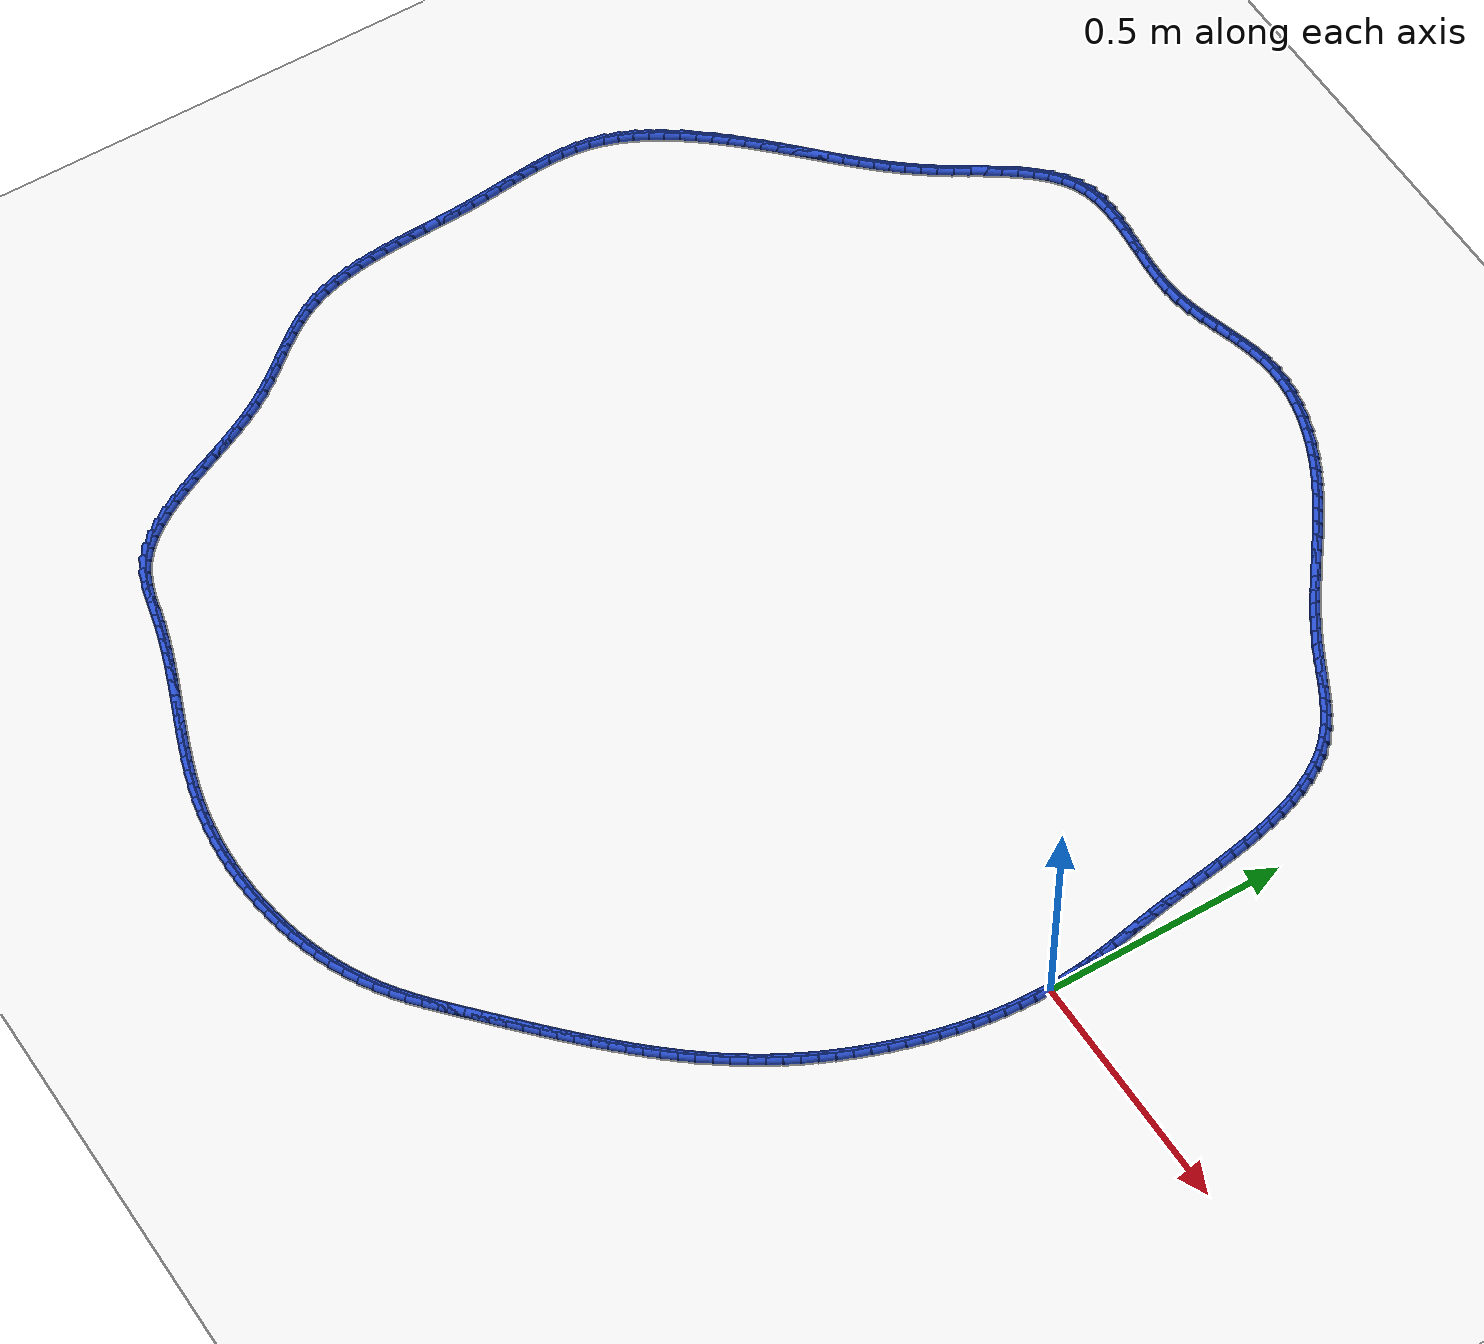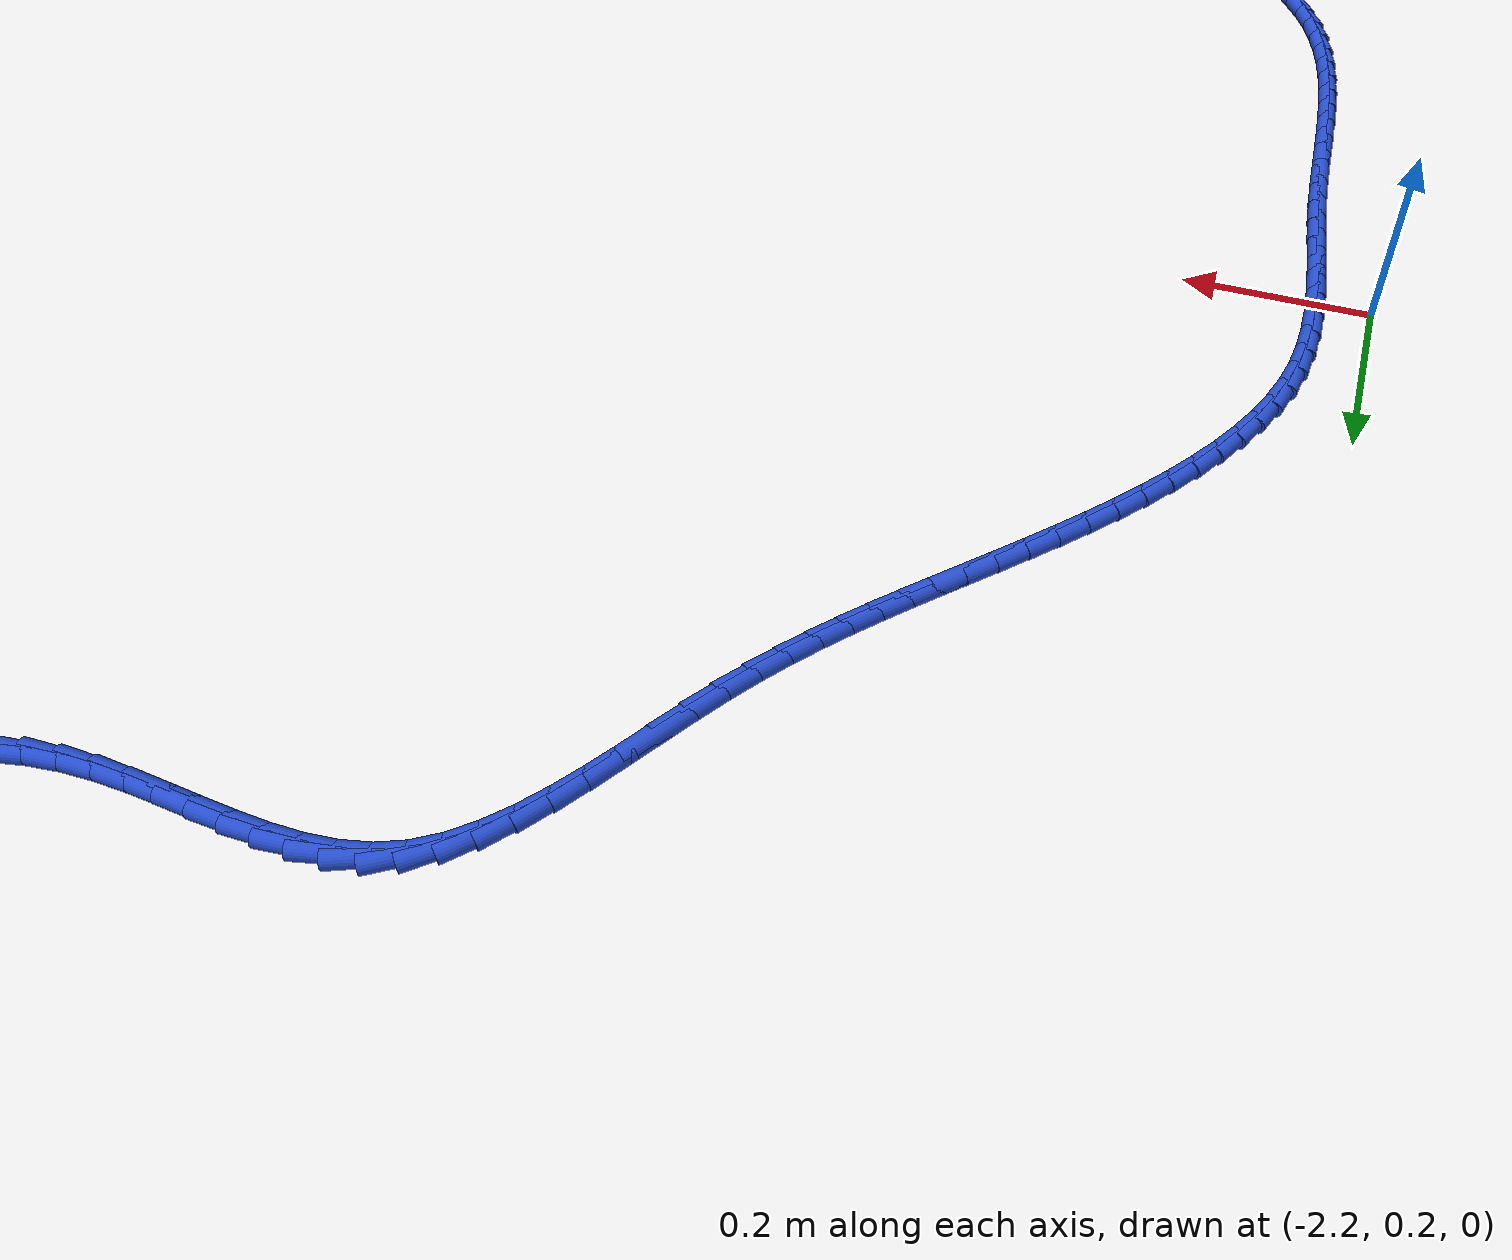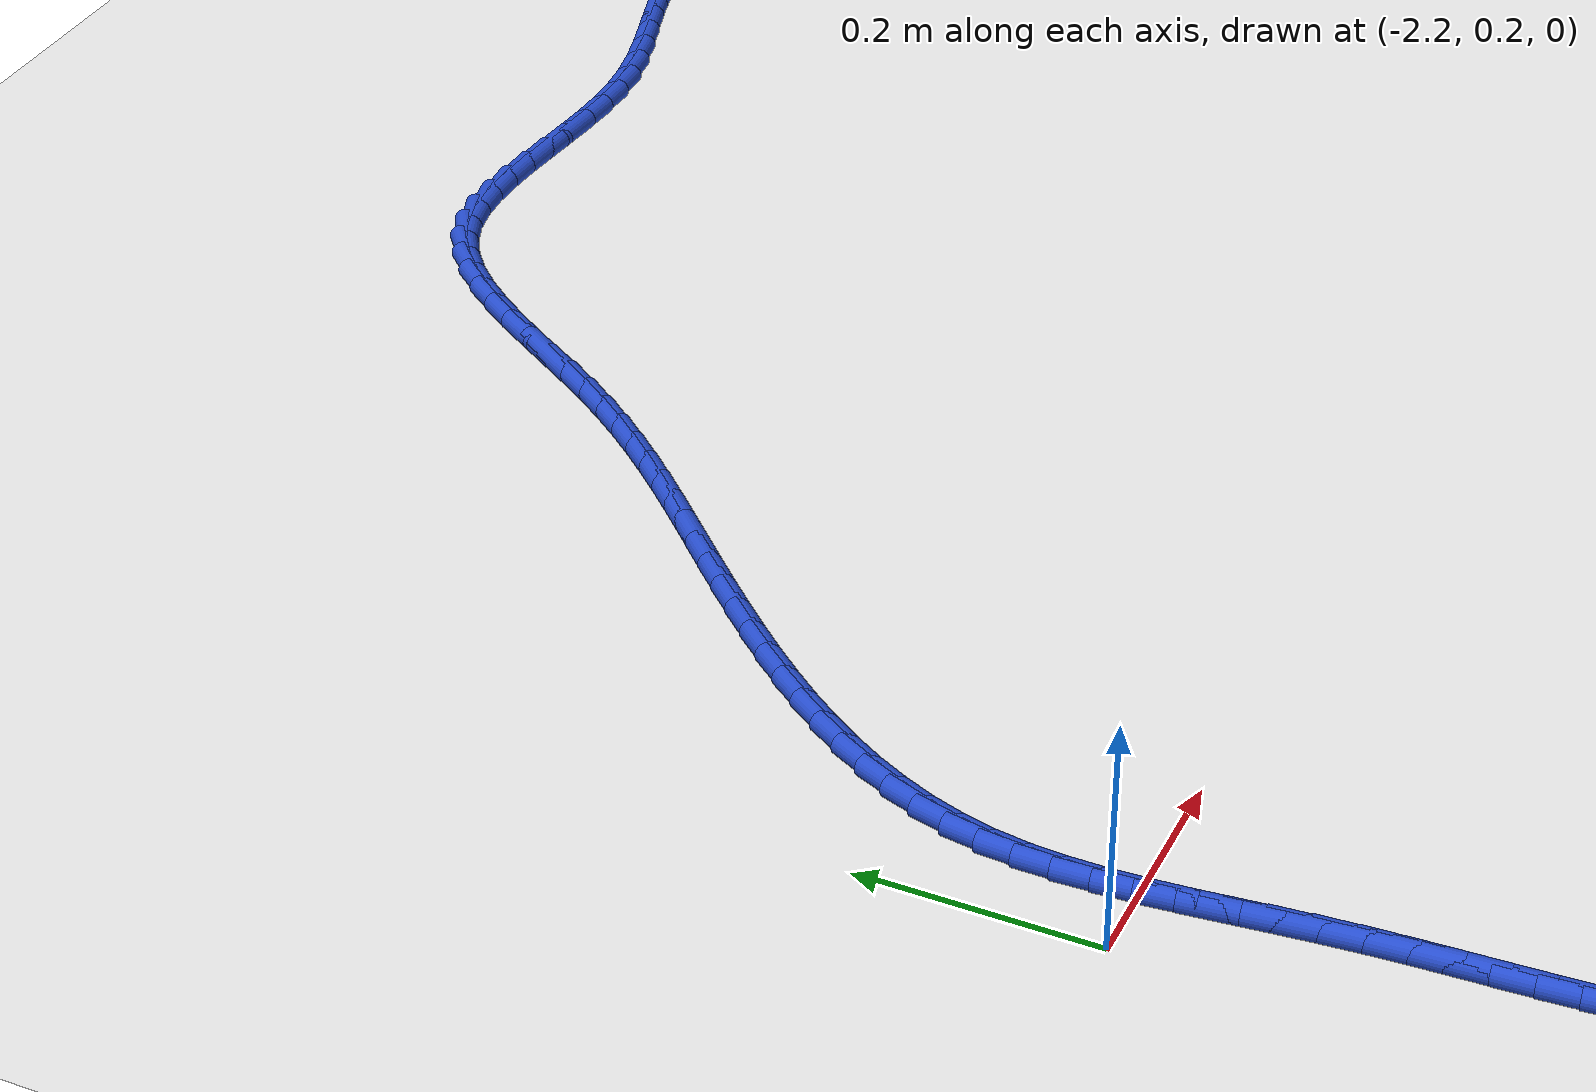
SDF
<sdf version="1.6">
 <world name="default">
  <light name="sun" type="directional">
   <pose>0 0 10 0 -0 0</pose>
   <diffuse>0.8 0.8 0.8 1</diffuse>
   <specular>0.2 0.2 0.2 1</specular>
   <attenuation>
    <range>1000</range>
    <constant>0.9</constant>
    <linear>0.01</linear>
    <quadratic>0.001</quadratic>
   </attenuation>
   <direction>-0.5 0.1 -0.9</direction>
  </light>
  <model name="ground_plane">
   <static>1</static>
   <link name="link">
    <collision name="collision">
     <geometry><plane><normal>0 0 1</normal><size>100 100</size></plane></geometry>
     <surface><friction><ode><mu>100</mu><mu2>50</mu2></ode></friction></surface>
    </collision>
    <visual name="visual">
     <cast_shadows>0</cast_shadows>
     <geometry><plane><normal>0 0 1</normal><size>100 100</size></plane></geometry>
     <material>
      <script><uri>file://media/materials/scripts/gazebo.material</uri><name>Gazebo/WhiteGlow</name></script>
     </material>
    </visual>
   </link>
  </model>
  <gravity>0 0 -9.8</gravity>
  <magnetic_field>6e-06 2.3e-05 -4.2e-05</magnetic_field>
  <atmosphere type="adiabatic"/>
  <physics name="default_physics" default="0" type="ode">
   <max_step_size>0.001</max_step_size>
   <real_time_factor>1</real_time_factor>
   <real_time_update_rate>1000</real_time_update_rate>
  </physics>
  <scene><ambient>0.4 0.4 0.4 1</ambient><background>0.7 0.7 0.7 1</background><shadows>1</shadows></scene>
  <spherical_coordinates>
   <surface_model>EARTH_WGS84</surface_model>
   <latitude_deg>0</latitude_deg>
   <longitude_deg>0</longitude_deg>
   <elevation>0</elevation>
   <heading_deg>0</heading_deg>
  </spherical_coordinates>
  <model name="line">
   <link name="link_0">
    <pose>1.9081958235744878e-17 2.7755575615628914e-17 0.01 0 1.57 -1.5188802915964286</pose>
    <collision name="collision">
     <geometry><cylinder><radius>0.01</radius><length>0.08</length></cylinder></geometry>
    </collision>
    <visual name="visual">
     <material>
      <script><name>Gazebo/Blue</name><uri>file://media/materials/scripts/gazebo.material</uri></script>
     </material>
     <geometry><cylinder><radius>0.01</radius><length>0.08</length></cylinder></geometry>
    </visual>
   </link>
   <link name="link_1">
    <pose>-0.00159963294675013 0.030784237129509895 0.01 0 1.57 -1.480813167682039</pose>
    <collision name="collision">
     <geometry><cylinder><radius>0.01</radius><length>0.08</length></cylinder></geometry>
    </collision>
    <visual name="visual">
     <material>
      <script><name>Gazebo/Blue</name><uri>file://media/materials/scripts/gazebo.material</uri></script>
     </material>
     <geometry><cylinder><radius>0.01</radius><length>0.08</length></cylinder></geometry>
    </visual>
   </link>
   <link name="link_2">
    <pose>-0.004365060638754378 0.06143397010637414 0.01 0 1.57 -1.4492488583605578</pose>
    <collision name="collision">
     <geometry><cylinder><radius>0.01</radius><length>0.08</length></cylinder></geometry>
    </collision>
    <visual name="visual">
     <material>
      <script><name>Gazebo/Blue</name><uri>file://media/materials/scripts/gazebo.material</uri></script>
     </material>
     <geometry><cylinder><radius>0.01</radius><length>0.08</length></cylinder></geometry>
    </visual>
   </link>
   <link name="link_3">
    <pose>-0.008102973358186778 0.09203507519566667 0.01 0 1.57 -1.4244183550075125</pose>
    <collision name="collision">
     <geometry><cylinder><radius>0.01</radius><length>0.08</length></cylinder></geometry>
    </collision>
    <visual name="visual">
     <material>
      <script><name>Gazebo/Blue</name><uri>file://media/materials/scripts/gazebo.material</uri></script>
     </material>
     <geometry><cylinder><radius>0.01</radius><length>0.08</length></cylinder></geometry>
    </visual>
   </link>
   <link name="link_4">
    <pose>-0.012620061387221403 0.12267342866246148 0.01 0 1.57 -1.406405570906267</pose>
    <collision name="collision">
     <geometry><cylinder><radius>0.01</radius><length>0.08</length></cylinder></geometry>
    </collision>
    <visual name="visual">
     <material>
      <script><name>Gazebo/Blue</name><uri>file://media/materials/scripts/gazebo.material</uri></script>
     </material>
     <geometry><cylinder><radius>0.01</radius><length>0.08</length></cylinder></geometry>
    </visual>
   </link>
   <link name="link_5">
    <pose>-0.0177230150080323 0.15343490677183247 0.01 0 1.57 -1.395180778490515</pose>
    <collision name="collision">
     <geometry><cylinder><radius>0.01</radius><length>0.08</length></cylinder></geometry>
    </collision>
    <visual name="visual">
     <material>
      <script><name>Gazebo/Blue</name><uri>file://media/materials/scripts/gazebo.material</uri></script>
     </material>
     <geometry><cylinder><radius>0.01</radius><length>0.08</length></cylinder></geometry>
    </visual>
   </link>
   <link name="link_6">
    <pose>-0.02321852450279352 0.1844053857888535 0.01 0 1.57 -1.3906287343230703</pose>
    <collision name="collision">
     <geometry><cylinder><radius>0.01</radius><length>0.08</length></cylinder></geometry>
    </collision>
    <visual name="visual">
     <material>
      <script><name>Gazebo/Blue</name><uri>file://media/materials/scripts/gazebo.material</uri></script>
     </material>
     <geometry><cylinder><radius>0.01</radius><length>0.08</length></cylinder></geometry>
    </visual>
   </link>
   <link name="link_7">
    <pose>-0.028913280153679125 0.2156707419785985 0.01 0 1.57 -1.3925689515927684</pose>
    <collision name="collision">
     <geometry><cylinder><radius>0.01</radius><length>0.08</length></cylinder></geometry>
    </collision>
    <visual name="visual">
     <material>
      <script><name>Gazebo/Blue</name><uri>file://media/materials/scripts/gazebo.material</uri></script>
     </material>
     <geometry><cylinder><radius>0.01</radius><length>0.08</length></cylinder></geometry>
    </visual>
   </link>
   <link name="link_8">
    <pose>-0.03461397224286319 0.24731685160614147 0.01 0 1.57 -1.4007676501543929</pose>
    <collision name="collision">
     <geometry><cylinder><radius>0.01</radius><length>0.08</length></cylinder></geometry>
    </collision>
    <visual name="visual">
     <material>
      <script><name>Gazebo/Blue</name><uri>file://media/materials/scripts/gazebo.material</uri></script>
     </material>
     <geometry><cylinder><radius>0.01</radius><length>0.08</length></cylinder></geometry>
    </visual>
   </link>
   <link name="link_9">
    <pose>-0.040127291052519755 0.2794295909365563 0.01 0 1.57 -1.4132256617355767</pose>
    <collision name="collision">
     <geometry><cylinder><radius>0.01</radius><length>0.08</length></cylinder></geometry>
    </collision>
    <visual name="visual">
     <material>
      <script><name>Gazebo/Blue</name><uri>file://media/materials/scripts/gazebo.material</uri></script>
     </material>
     <geometry><cylinder><radius>0.01</radius><length>0.08</length></cylinder></geometry>
    </visual>
   </link>
   <link name="link_10">
    <pose>-0.04531178999527231 0.3120595220701327 0.01 0 1.57 -1.4213807271817895</pose>
    <collision name="collision">
     <geometry><cylinder><radius>0.01</radius><length>0.08</length></cylinder></geometry>
    </collision>
    <visual name="visual">
     <material>
      <script><name>Gazebo/Blue</name><uri>file://media/materials/scripts/gazebo.material</uri></script>
     </material>
     <geometry><cylinder><radius>0.01</radius><length>0.08</length></cylinder></geometry>
    </visual>
   </link>
   <link name="link_11">
    <pose>-0.050282951342190824 0.34508226147687576 0.01 0 1.57 -1.422872848550074</pose>
    <collision name="collision">
     <geometry><cylinder><radius>0.01</radius><length>0.08</length></cylinder></geometry>
    </collision>
    <visual name="visual">
     <material>
      <script><name>Gazebo/Blue</name><uri>file://media/materials/scripts/gazebo.material</uri></script>
     </material>
     <geometry><cylinder><radius>0.01</radius><length>0.08</length></cylinder></geometry>
    </visual>
   </link>
   <link name="link_12">
    <pose>-0.0552356739835631 0.3783193499943837 0.01 0 1.57 -1.4178449396806017</pose>
    <collision name="collision">
     <geometry><cylinder><radius>0.01</radius><length>0.08</length></cylinder></geometry>
    </collision>
    <visual name="visual">
     <material>
      <script><name>Gazebo/Blue</name><uri>file://media/materials/scripts/gazebo.material</uri></script>
     </material>
     <geometry><cylinder><radius>0.01</radius><length>0.08</length></cylinder></geometry>
    </visual>
   </link>
   <link name="link_13">
    <pose>-0.06036488005807191 0.41159231263017193 0.01 0 1.57 -1.406267828261708</pose>
    <collision name="collision">
     <geometry><cylinder><radius>0.01</radius><length>0.08</length></cylinder></geometry>
    </collision>
    <visual name="visual">
     <material>
      <script><name>Gazebo/Blue</name><uri>file://media/materials/scripts/gazebo.material</uri></script>
     </material>
     <geometry><cylinder><radius>0.01</radius><length>0.08</length></cylinder></geometry>
    </visual>
   </link>
   <link name="link_14">
    <pose>-0.06586549170440008 0.44472267439175545 0.01 0 1.57 -1.387946446707864</pose>
    <collision name="collision">
     <geometry><cylinder><radius>0.01</radius><length>0.08</length></cylinder></geometry>
    </collision>
    <visual name="visual">
     <material>
      <script><name>Gazebo/Blue</name><uri>file://media/materials/scripts/gazebo.material</uri></script>
     </material>
     <geometry><cylinder><radius>0.01</radius><length>0.08</length></cylinder></geometry>
    </visual>
   </link>
   <link name="link_15">
    <pose>-0.0719324310612304 0.47753196028664974 0.01 0 1.57 -1.3625255270032168</pose>
    <collision name="collision">
     <geometry><cylinder><radius>0.01</radius><length>0.08</length></cylinder></geometry>
    </collision>
    <visual name="visual">
     <material>
      <script><name>Gazebo/Blue</name><uri>file://media/materials/scripts/gazebo.material</uri></script>
     </material>
     <geometry><cylinder><radius>0.01</radius><length>0.08</length></cylinder></geometry>
    </visual>
   </link>
   <link name="link_16">
    <pose>-0.07876062026724572 0.5098416953223701 0.01 0 1.57 -1.3294976411010102</pose>
    <collision name="collision">
     <geometry><cylinder><radius>0.01</radius><length>0.08</length></cylinder></geometry>
    </collision>
    <visual name="visual">
     <material>
      <script><name>Gazebo/Blue</name><uri>file://media/materials/scripts/gazebo.material</uri></script>
     </material>
     <geometry><cylinder><radius>0.01</radius><length>0.08</length></cylinder></geometry>
    </visual>
   </link>
   <link name="link_17">
    <pose>-0.08654498146112878 0.5414734045064316 0.01 0 1.57 -1.2882198751110274</pose>
    <collision name="collision">
     <geometry><cylinder><radius>0.01</radius><length>0.08</length></cylinder></geometry>
    </collision>
    <visual name="visual">
     <material>
      <script><name>Gazebo/Blue</name><uri>file://media/materials/scripts/gazebo.material</uri></script>
     </material>
     <geometry><cylinder><radius>0.01</radius><length>0.08</length></cylinder></geometry>
    </visual>
   </link>
   <link name="link_18">
    <pose>-0.09548043678156241 0.5722486128463496 0.01 0 1.57 -1.237949160713383</pose>
    <collision name="collision">
     <geometry><cylinder><radius>0.01</radius><length>0.08</length></cylinder></geometry>
    </collision>
    <visual name="visual">
     <material>
      <script><name>Gazebo/Blue</name><uri>file://media/materials/scripts/gazebo.material</uri></script>
     </material>
     <geometry><cylinder><radius>0.01</radius><length>0.08</length></cylinder></geometry>
    </visual>
   </link>
   <link name="link_19">
    <pose>-0.10576190836722948 0.6019888453496396 0.01 0 1.57 -1.1779108470160669</pose>
    <collision name="collision">
     <geometry><cylinder><radius>0.01</radius><length>0.08</length></cylinder></geometry>
    </collision>
    <visual name="visual">
     <material>
      <script><name>Gazebo/Blue</name><uri>file://media/materials/scripts/gazebo.material</uri></script>
     </material>
     <geometry><cylinder><radius>0.01</radius><length>0.08</length></cylinder></geometry>
    </visual>
   </link>
   <link name="link_20">
    <pose>-0.11758431835681268 0.6305156270238166 0.01 0 1.57 -1.107418735966026</pose>
    <collision name="collision">
     <geometry><cylinder><radius>0.01</radius><length>0.08</length></cylinder></geometry>
    </collision>
    <visual name="visual">
     <material>
      <script><name>Gazebo/Blue</name><uri>file://media/materials/scripts/gazebo.material</uri></script>
     </material>
     <geometry><cylinder><radius>0.01</radius><length>0.08</length></cylinder></geometry>
    </visual>
   </link>
   <link name="link_21">
    <pose>-0.13114258888899485 0.6576504828763958 0.01 0 1.57 -1.0260627595932994</pose>
    <collision name="collision">
     <geometry><cylinder><radius>0.01</radius><length>0.08</length></cylinder></geometry>
    </collision>
    <visual name="visual">
     <material>
      <script><name>Gazebo/Blue</name><uri>file://media/materials/scripts/gazebo.material</uri></script>
     </material>
     <geometry><cylinder><radius>0.01</radius><length>0.08</length></cylinder></geometry>
    </visual>
   </link>
   <link name="link_22">
    <pose>-0.14663164210245885 0.6832149379148926 0.01 0 1.57 -0.9339640023764577</pose>
    <collision name="collision">
     <geometry><cylinder><radius>0.01</radius><length>0.08</length></cylinder></geometry>
    </collision>
    <visual name="visual">
     <material>
      <script><name>Gazebo/Blue</name><uri>file://media/materials/scripts/gazebo.material</uri></script>
     </material>
     <geometry><cylinder><radius>0.01</radius><length>0.08</length></cylinder></geometry>
    </visual>
   </link>
   <link name="link_23">
    <pose>-0.1642464001358875 0.7070305171468226 0.01 0 1.57 -0.8320566405855585</pose>
    <collision name="collision">
     <geometry><cylinder><radius>0.01</radius><length>0.08</length></cylinder></geometry>
    </collision>
    <visual name="visual">
     <material>
      <script><name>Gazebo/Blue</name><uri>file://media/materials/scripts/gazebo.material</uri></script>
     </material>
     <geometry><cylinder><radius>0.01</radius><length>0.08</length></cylinder></geometry>
    </visual>
   </link>
   <link name="link_24">
    <pose>-0.18418178512796354 0.7289187455797006 0.01 0 1.57 -0.7244999463171347</pose>
    <collision name="collision">
     <geometry><cylinder><radius>0.01</radius><length>0.08</length></cylinder></geometry>
    </collision>
    <visual name="visual">
     <material>
      <script><name>Gazebo/Blue</name><uri>file://media/materials/scripts/gazebo.material</uri></script>
     </material>
     <geometry><cylinder><radius>0.01</radius><length>0.08</length></cylinder></geometry>
    </visual>
   </link>
   <link name="link_25">
    <pose>-0.20658356720739174 0.7487456897266181 0.01 0 1.57 -0.6322358763020309</pose>
    <collision name="collision">
     <geometry><cylinder><radius>0.01</radius><length>0.08</length></cylinder></geometry>
    </collision>
    <visual name="visual">
     <material>
      <script><name>Gazebo/Blue</name><uri>file://media/materials/scripts/gazebo.material</uri></script>
     </material>
     <geometry><cylinder><radius>0.01</radius><length>0.08</length></cylinder></geometry>
    </visual>
   </link>
   <link name="link_26">
    <pose>-0.23117517323548958 0.7667601431754679 0.01 0 1.57 -0.5644500898084038</pose>
    <collision name="collision">
     <geometry><cylinder><radius>0.01</radius><length>0.08</length></cylinder></geometry>
    </collision>
    <visual name="visual">
     <material>
      <script><name>Gazebo/Blue</name><uri>file://media/materials/scripts/gazebo.material</uri></script>
     </material>
     <geometry><cylinder><radius>0.01</radius><length>0.08</length></cylinder></geometry>
    </visual>
   </link>
   <link name="link_27">
    <pose>-0.25746486162807614 0.7834058849586697 0.01 0 1.57 -0.519456450435166</pose>
    <collision name="collision">
     <geometry><cylinder><radius>0.01</radius><length>0.08</length></cylinder></geometry>
    </collision>
    <visual name="visual">
     <material>
      <script><name>Gazebo/Blue</name><uri>file://media/materials/scripts/gazebo.material</uri></script>
     </material>
     <geometry><cylinder><radius>0.01</radius><length>0.08</length></cylinder></geometry>
    </visual>
   </link>
   <link name="link_28">
    <pose>-0.28495917986475866 0.7991282445574422 0.01 0 1.57 -0.4954993511850431</pose>
    <collision name="collision">
     <geometry><cylinder><radius>0.01</radius><length>0.08</length></cylinder></geometry>
    </collision>
    <visual name="visual">
     <material>
      <script><name>Gazebo/Blue</name><uri>file://media/materials/scripts/gazebo.material</uri></script>
     </material>
     <geometry><cylinder><radius>0.01</radius><length>0.08</length></cylinder></geometry>
    </visual>
   </link>
   <link name="link_29">
    <pose>-0.3131646754251447 0.8143725514530047 0.01 0 1.57 -0.49139515971351777</pose>
    <collision name="collision">
     <geometry><cylinder><radius>0.01</radius><length>0.08</length></cylinder></geometry>
    </collision>
    <visual name="visual">
     <material>
      <script><name>Gazebo/Blue</name><uri>file://media/materials/scripts/gazebo.material</uri></script>
     </material>
     <geometry><cylinder><radius>0.01</radius><length>0.08</length></cylinder></geometry>
    </visual>
   </link>
   <link name="link_30">
    <pose>-0.3415878957888413 0.8295841351265755 0.01 0 1.57 -0.5067371997710283</pose>
    <collision name="collision">
     <geometry><cylinder><radius>0.01</radius><length>0.08</length></cylinder></geometry>
    </collision>
    <visual name="visual">
     <material>
      <script><name>Gazebo/Blue</name><uri>file://media/materials/scripts/gazebo.material</uri></script>
     </material>
     <geometry><cylinder><radius>0.01</radius><length>0.08</length></cylinder></geometry>
    </visual>
   </link>
   <link name="link_31">
    <pose>-0.3697353884354559 0.8452083250593737 0.01 0 1.57 -0.5392300308553891</pose>
    <collision name="collision">
     <geometry><cylinder><radius>0.01</radius><length>0.08</length></cylinder></geometry>
    </collision>
    <visual name="visual">
     <material>
      <script><name>Gazebo/Blue</name><uri>file://media/materials/scripts/gazebo.material</uri></script>
     </material>
     <geometry><cylinder><radius>0.01</radius><length>0.08</length></cylinder></geometry>
    </visual>
   </link>
   <link name="link_32">
    <pose>-0.39717732171991554 0.861629124445607 0.01 0 1.57 -0.5725438408554816</pose>
    <collision name="collision">
     <geometry><cylinder><radius>0.01</radius><length>0.08</length></cylinder></geometry>
    </collision>
    <visual name="visual">
     <material>
      <script><name>Gazebo/Blue</name><uri>file://media/materials/scripts/gazebo.material</uri></script>
     </material>
     <geometry><cylinder><radius>0.01</radius><length>0.08</length></cylinder></geometry>
    </visual>
   </link>
   <link name="link_33">
    <pose>-0.42388497039961287 0.8788438966189673 0.01 0 1.57 -0.5999865828646224</pose>
    <collision name="collision">
     <geometry><cylinder><radius>0.01</radius><length>0.08</length></cylinder></geometry>
    </collision>
    <visual name="visual">
     <material>
      <script><name>Gazebo/Blue</name><uri>file://media/materials/scripts/gazebo.material</uri></script>
     </material>
     <geometry><cylinder><radius>0.01</radius><length>0.08</length></cylinder></geometry>
    </visual>
   </link>
   <link name="link_34">
    <pose>-0.4499855127751435 0.8966997242798087 0.01 0 1.57 -0.6213584745861429</pose>
    <collision name="collision">
     <geometry><cylinder><radius>0.01</radius><length>0.08</length></cylinder></geometry>
    </collision>
    <visual name="visual">
     <material>
      <script><name>Gazebo/Blue</name><uri>file://media/materials/scripts/gazebo.material</uri></script>
     </material>
     <geometry><cylinder><radius>0.01</radius><length>0.08</length></cylinder></geometry>
    </visual>
   </link>
   <link name="link_35">
    <pose>-0.47560647454656535 0.9150433552585392 0.01 0 1.57 -0.6365380052178342</pose>
    <collision name="collision">
     <geometry><cylinder><radius>0.01</radius><length>0.08</length></cylinder></geometry>
    </collision>
    <visual name="visual">
     <material>
      <script><name>Gazebo/Blue</name><uri>file://media/materials/scripts/gazebo.material</uri></script>
     </material>
     <geometry><cylinder><radius>0.01</radius><length>0.08</length></cylinder></geometry>
    </visual>
   </link>
   <link name="link_36">
    <pose>-0.5008753814139361 0.9337215373855666 0.01 0 1.57 -0.6454454754408275</pose>
    <collision name="collision">
     <geometry><cylinder><radius>0.01</radius><length>0.08</length></cylinder></geometry>
    </collision>
    <visual name="visual">
     <material>
      <script><name>Gazebo/Blue</name><uri>file://media/materials/scripts/gazebo.material</uri></script>
     </material>
     <geometry><cylinder><radius>0.01</radius><length>0.08</length></cylinder></geometry>
    </visual>
   </link>
   <link name="link_37">
    <pose>-0.5259197590773135 0.9525810184912994 0.01 0 1.57 -0.648026356055063</pose>
    <collision name="collision">
     <geometry><cylinder><radius>0.01</radius><length>0.08</length></cylinder></geometry>
    </collision>
    <visual name="visual">
     <material>
      <script><name>Gazebo/Blue</name><uri>file://media/materials/scripts/gazebo.material</uri></script>
     </material>
     <geometry><cylinder><radius>0.01</radius><length>0.08</length></cylinder></geometry>
    </visual>
   </link>
   <link name="link_38">
    <pose>-0.5508671332367554 0.9714685464061453 0.01 0 1.57 -0.6442411997056904</pose>
    <collision name="collision">
     <geometry><cylinder><radius>0.01</radius><length>0.08</length></cylinder></geometry>
    </collision>
    <visual name="visual">
     <material>
      <script><name>Gazebo/Blue</name><uri>file://media/materials/scripts/gazebo.material</uri></script>
     </material>
     <geometry><cylinder><radius>0.01</radius><length>0.08</length></cylinder></geometry>
    </visual>
   </link>
   <link name="link_39">
    <pose>-0.5758450295923194 0.9902308689605123 0.01 0 1.57 -0.6340628227858532</pose>
    <collision name="collision">
     <geometry><cylinder><radius>0.01</radius><length>0.08</length></cylinder></geometry>
    </collision>
    <visual name="visual">
     <material>
      <script><name>Gazebo/Blue</name><uri>file://media/materials/scripts/gazebo.material</uri></script>
     </material>
     <geometry><cylinder><radius>0.01</radius><length>0.08</length></cylinder></geometry>
    </visual>
   </link>
   <link name="link_40">
    <pose>-0.6009809738440636 1.0087147339848086 0.01 0 1.57 -0.6174811470293351</pose>
    <collision name="collision">
     <geometry><cylinder><radius>0.01</radius><length>0.08</length></cylinder></geometry>
    </collision>
    <visual name="visual">
     <material>
      <script><name>Gazebo/Blue</name><uri>file://media/materials/scripts/gazebo.material</uri></script>
     </material>
     <geometry><cylinder><radius>0.01</radius><length>0.08</length></cylinder></geometry>
    </visual>
   </link>
   <link name="link_41">
    <pose>-0.6264024916920453 1.0267668893094417 0.01 0 1.57 -0.5945158301193204</pose>
    <collision name="collision">
     <geometry><cylinder><radius>0.01</radius><length>0.08</length></cylinder></geometry>
    </collision>
    <visual name="visual">
     <material>
      <script><name>Gazebo/Blue</name><uri>file://media/materials/scripts/gazebo.material</uri></script>
     </material>
     <geometry><cylinder><radius>0.01</radius><length>0.08</length></cylinder></geometry>
    </visual>
   </link>
   <link name="link_42">
    <pose>-0.6522371088363226 1.0442340827648202 0.01 0 1.57 -0.5652363997656895</pose>
    <collision name="collision">
     <geometry><cylinder><radius>0.01</radius><length>0.08</length></cylinder></geometry>
    </collision>
    <visual name="visual">
     <material>
      <script><name>Gazebo/Blue</name><uri>file://media/materials/scripts/gazebo.material</uri></script>
     </material>
     <geometry><cylinder><radius>0.01</radius><length>0.08</length></cylinder></geometry>
    </visual>
   </link>
   <link name="link_43">
    <pose>-0.6786123509769534 1.0609630621813522 0.01 0 1.57 -0.5297888180299466</pose>
    <collision name="collision">
     <geometry><cylinder><radius>0.01</radius><length>0.08</length></cylinder></geometry>
    </collision>
    <visual name="visual">
     <material>
      <script><name>Gazebo/Blue</name><uri>file://media/materials/scripts/gazebo.material</uri></script>
     </material>
     <geometry><cylinder><radius>0.01</radius><length>0.08</length></cylinder></geometry>
    </visual>
   </link>
   <link name="link_44">
    <pose>-0.705655743813995 1.076800575389445 0.01 0 1.57 -0.4884260941336253</pose>
    <collision name="collision">
     <geometry><cylinder><radius>0.01</radius><length>0.08</length></cylinder></geometry>
    </collision>
    <visual name="visual">
     <material>
      <script><name>Gazebo/Blue</name><uri>file://media/materials/scripts/gazebo.material</uri></script>
     </material>
     <geometry><cylinder><radius>0.01</radius><length>0.08</length></cylinder></geometry>
    </visual>
   </link>
   <link name="link_45">
    <pose>-0.7334948130475054 1.091593370219507 0.01 0 1.57 -0.44154401655973075</pose>
    <collision name="collision">
     <geometry><cylinder><radius>0.01</radius><length>0.08</length></cylinder></geometry>
    </collision>
    <visual name="visual">
     <material>
      <script><name>Gazebo/Blue</name><uri>file://media/materials/scripts/gazebo.material</uri></script>
     </material>
     <geometry><cylinder><radius>0.01</radius><length>0.08</length></cylinder></geometry>
    </visual>
   </link>
   <link name="link_46">
    <pose>-0.7622542614769345 1.1051870447690146 0.01 0 1.57 -0.3896931485471</pose>
    <collision name="collision">
     <geometry><cylinder><radius>0.01</radius><length>0.08</length></cylinder></geometry>
    </collision>
    <visual name="visual">
     <material>
      <script><name>Gazebo/Blue</name><uri>file://media/materials/scripts/gazebo.material</uri></script>
     </material>
     <geometry><cylinder><radius>0.01</radius><length>0.08</length></cylinder></geometry>
    </visual>
   </link>
   <link name="link_47">
    <pose>-0.7919247577532474 1.1173726066641576 0.01 0 1.57 -0.33248504168207843</pose>
    <collision name="collision">
     <geometry><cylinder><radius>0.01</radius><length>0.08</length></cylinder></geometry>
    </collision>
    <visual name="visual">
     <material>
      <script><name>Gazebo/Blue</name><uri>file://media/materials/scripts/gazebo.material</uri></script>
     </material>
     <geometry><cylinder><radius>0.01</radius><length>0.08</length></cylinder></geometry>
    </visual>
   </link>
   <link name="link_48">
    <pose>-0.8223073312080927 1.1278638257530509 0.01 0 1.57 -0.2687404948337519</pose>
    <collision name="collision">
     <geometry><cylinder><radius>0.01</radius><length>0.08</length></cylinder></geometry>
    </collision>
    <visual name="visual">
     <material>
      <script><name>Gazebo/Blue</name><uri>file://media/materials/scripts/gazebo.material</uri></script>
     </material>
     <geometry><cylinder><radius>0.01</radius><length>0.08</length></cylinder></geometry>
    </visual>
   </link>
   <link name="link_49">
    <pose>-0.8531886456904374 1.1363686209982045 0.01 0 1.57 -0.19717793944265907</pose>
    <collision name="collision">
     <geometry><cylinder><radius>0.01</radius><length>0.08</length></cylinder></geometry>
    </collision>
    <visual name="visual">
     <material>
      <script><name>Gazebo/Blue</name><uri>file://media/materials/scripts/gazebo.material</uri></script>
     </material>
     <geometry><cylinder><radius>0.01</radius><length>0.08</length></cylinder></geometry>
    </visual>
   </link>
   <link name="link_50">
    <pose>-0.8843553650492477 1.1425949113621277 0.01 0 1.57 -0.11649466862774568</pose>
    <collision name="collision">
     <geometry><cylinder><radius>0.01</radius><length>0.08</length></cylinder></geometry>
    </collision>
    <visual name="visual">
     <material>
      <script><name>Gazebo/Blue</name><uri>file://media/materials/scripts/gazebo.material</uri></script>
     </material>
     <geometry><cylinder><radius>0.01</radius><length>0.08</length></cylinder></geometry>
    </visual>
   </link>
   <link name="link_51">
    <pose>-0.9155941531334906 1.1462506158073302 0.01 0 1.57 -0.025496104717886242</pose>
    <collision name="collision">
     <geometry><cylinder><radius>0.01</radius><length>0.08</length></cylinder></geometry>
    </collision>
    <visual name="visual">
     <material>
      <script><name>Gazebo/Blue</name><uri>file://media/materials/scripts/gazebo.material</uri></script>
     </material>
     <geometry><cylinder><radius>0.01</radius><length>0.08</length></cylinder></geometry>
    </visual>
   </link>
   <link name="link_52">
    <pose>-0.9466916737921333 1.147043653296322 0.01 0 1.57 0.07595522961773309</pose>
    <collision name="collision">
     <geometry><cylinder><radius>0.01</radius><length>0.08</length></cylinder></geometry>
    </collision>
    <visual name="visual">
     <material>
      <script><name>Gazebo/Blue</name><uri>file://media/materials/scripts/gazebo.material</uri></script>
     </material>
     <geometry><cylinder><radius>0.01</radius><length>0.08</length></cylinder></geometry>
    </visual>
   </link>
   <link name="link_53">
    <pose>-0.9774419042992067 1.1447035104973542 0.01 0 1.57 0.17045092742547432</pose>
    <collision name="collision">
     <geometry><cylinder><radius>0.01</radius><length>0.08</length></cylinder></geometry>
    </collision>
    <visual name="visual">
     <material>
      <script><name>Gazebo/Blue</name><uri>file://media/materials/scripts/gazebo.material</uri></script>
     </material>
     <geometry><cylinder><radius>0.01</radius><length>0.08</length></cylinder></geometry>
    </visual>
   </link>
   <link name="link_54">
    <pose>-1.0078138553914406 1.1394758576978292 0.01 0 1.57 0.23892675052437815</pose>
    <collision name="collision">
     <geometry><cylinder><radius>0.01</radius><length>0.08</length></cylinder></geometry>
    </collision>
    <visual name="visual">
     <material>
      <script><name>Gazebo/Blue</name><uri>file://media/materials/scripts/gazebo.material</uri></script>
     </material>
     <geometry><cylinder><radius>0.01</radius><length>0.08</length></cylinder></geometry>
    </visual>
   </link>
   <link name="link_55">
    <pose>-1.0379554488708378 1.1321339840744558 0.01 0 1.57 0.2803987848785397</pose>
    <collision name="collision">
     <geometry><cylinder><radius>0.01</radius><length>0.08</length></cylinder></geometry>
    </collision>
    <visual name="visual">
     <material>
      <script><name>Gazebo/Blue</name><uri>file://media/materials/scripts/gazebo.material</uri></script>
     </material>
     <geometry><cylinder><radius>0.01</radius><length>0.08</length></cylinder></geometry>
    </visual>
   </link>
   <link name="link_56">
    <pose>-1.0680226956017076 1.1234750339079418 0.01 0 1.57 0.2955357587619733</pose>
    <collision name="collision">
     <geometry><cylinder><radius>0.01</radius><length>0.08</length></cylinder></geometry>
    </collision>
    <visual name="visual">
     <material>
      <script><name>Gazebo/Blue</name><uri>file://media/materials/scripts/gazebo.material</uri></script>
     </material>
     <geometry><cylinder><radius>0.01</radius><length>0.08</length></cylinder></geometry>
    </visual>
   </link>
   <link name="link_57">
    <pose>-1.0981716064483589 1.1142961514789969 0.01 0 1.57 0.2849739989582786</pose>
    <collision name="collision">
     <geometry><cylinder><radius>0.01</radius><length>0.08</length></cylinder></geometry>
    </collision>
    <visual name="visual">
     <material>
      <script><name>Gazebo/Blue</name><uri>file://media/materials/scripts/gazebo.material</uri></script>
     </material>
     <geometry><cylinder><radius>0.01</radius><length>0.08</length></cylinder></geometry>
    </visual>
   </link>
   <link name="link_58">
    <pose>-1.1285581922751007 1.10539448106833 0.01 0 1.57 0.24901828403818713</pose>
    <collision name="collision">
     <geometry><cylinder><radius>0.01</radius><length>0.08</length></cylinder></geometry>
    </collision>
    <visual name="visual">
     <material>
      <script><name>Gazebo/Blue</name><uri>file://media/materials/scripts/gazebo.material</uri></script>
     </material>
     <geometry><cylinder><radius>0.01</radius><length>0.08</length></cylinder></geometry>
    </visual>
   </link>
   <link name="link_59">
    <pose>-1.1593384639462412 1.0975671669566491 0.01 0 1.57 0.18785804597891959</pose>
    <collision name="collision">
     <geometry><cylinder><radius>0.01</radius><length>0.08</length></cylinder></geometry>
    </collision>
    <visual name="visual">
     <material>
      <script><name>Gazebo/Blue</name><uri>file://media/materials/scripts/gazebo.material</uri></script>
     </material>
     <geometry><cylinder><radius>0.01</radius><length>0.08</length></cylinder></geometry>
    </visual>
   </link>
   <link name="link_60">
    <pose>-1.1906684323260897 1.091611353424664 0.01 0 1.57 0.10277971191584295</pose>
    <collision name="collision">
     <geometry><cylinder><radius>0.01</radius><length>0.08</length></cylinder></geometry>
    </collision>
    <visual name="visual">
     <material>
      <script><name>Gazebo/Blue</name><uri>file://media/materials/scripts/gazebo.material</uri></script>
     </material>
     <geometry><cylinder><radius>0.01</radius><length>0.08</length></cylinder></geometry>
    </visual>
   </link>
   <link name="link_61">
    <pose>-1.2226995123110567 1.0883075666803956 0.01 0 1.57 0.016059116760396376</pose>
    <collision name="collision">
     <geometry><cylinder><radius>0.01</radius><length>0.08</length></cylinder></geometry>
    </collision>
    <visual name="visual">
     <material>
      <script><name>Gazebo/Blue</name><uri>file://media/materials/scripts/gazebo.material</uri></script>
     </material>
     <geometry><cylinder><radius>0.01</radius><length>0.08</length></cylinder></geometry>
    </visual>
   </link>
   <link name="link_62">
    <pose>-1.2554022488459764 1.0877823444644523 0.01 0 1.57 -0.04604871069688419</pose>
    <collision name="collision">
     <geometry><cylinder><radius>0.01</radius><length>0.08</length></cylinder></geometry>
    </collision>
    <visual name="visual">
     <material>
      <script><name>Gazebo/Blue</name><uri>file://media/materials/scripts/gazebo.material</uri></script>
     </material>
     <geometry><cylinder><radius>0.01</radius><length>0.08</length></cylinder></geometry>
    </visual>
   </link>
   <link name="link_63">
    <pose>-1.288510948698966 1.0893080359593565 0.01 0 1.57 -0.08379796268698758</pose>
    <collision name="collision">
     <geometry><cylinder><radius>0.01</radius><length>0.08</length></cylinder></geometry>
    </collision>
    <visual name="visual">
     <material>
      <script><name>Gazebo/Blue</name><uri>file://media/materials/scripts/gazebo.material</uri></script>
     </material>
     <geometry><cylinder><radius>0.01</radius><length>0.08</length></cylinder></geometry>
    </visual>
   </link>
   <link name="link_64">
    <pose>-1.321744000851151 1.0920994349105482 0.01 0 1.57 -0.09860050907768565</pose>
    <collision name="collision">
     <geometry><cylinder><radius>0.01</radius><length>0.08</length></cylinder></geometry>
    </collision>
    <visual name="visual">
     <material>
      <script><name>Gazebo/Blue</name><uri>file://media/materials/scripts/gazebo.material</uri></script>
     </material>
     <geometry><cylinder><radius>0.01</radius><length>0.08</length></cylinder></geometry>
    </visual>
   </link>
   <link name="link_65">
    <pose>-1.3548197942836582 1.0953713350634695 0.01 0 1.57 -0.09066602689863554</pose>
    <collision name="collision">
     <geometry><cylinder><radius>0.01</radius><length>0.08</length></cylinder></geometry>
    </collision>
    <visual name="visual">
     <material>
      <script><name>Gazebo/Blue</name><uri>file://media/materials/scripts/gazebo.material</uri></script>
     </material>
     <geometry><cylinder><radius>0.01</radius><length>0.08</length></cylinder></geometry>
    </visual>
   </link>
   <link name="link_66">
    <pose>-1.3874567179776145 1.0983385301635609 0.01 0 1.57 -0.05875101340758058</pose>
    <collision name="collision">
     <geometry><cylinder><radius>0.01</radius><length>0.08</length></cylinder></geometry>
    </collision>
    <visual name="visual">
     <material>
      <script><name>Gazebo/Blue</name><uri>file://media/materials/scripts/gazebo.material</uri></script>
     </material>
     <geometry><cylinder><radius>0.01</radius><length>0.08</length></cylinder></geometry>
    </visual>
   </link>
   <link name="link_67">
    <pose>-1.4193731609141456 1.1002158139562634 0.01 0 1.57 -7.007201091386498e-05</pose>
    <collision name="collision">
     <geometry><cylinder><radius>0.01</radius><length>0.08</length></cylinder></geometry>
    </collision>
    <visual name="visual">
     <material>
      <script><name>Gazebo/Blue</name><uri>file://media/materials/scripts/gazebo.material</uri></script>
     </material>
     <geometry><cylinder><radius>0.01</radius><length>0.08</length></cylinder></geometry>
    </visual>
   </link>
   <link name="link_68">
    <pose>-1.4502875120743794 1.1002179801870189 0.01 0 1.57 0.08947023308897722</pose>
    <collision name="collision">
     <geometry><cylinder><radius>0.01</radius><length>0.08</length></cylinder></geometry>
    </collision>
    <visual name="visual">
     <material>
      <script><name>Gazebo/Blue</name><uri>file://media/materials/scripts/gazebo.material</uri></script>
     </material>
     <geometry><cylinder><radius>0.01</radius><length>0.08</length></cylinder></geometry>
    </visual>
   </link>
   <link name="link_69">
    <pose>-1.4799181604394418 1.0975598226012677 0.01 0 1.57 0.21414669175013792</pose>
    <collision name="collision">
     <geometry><cylinder><radius>0.01</radius><length>0.08</length></cylinder></geometry>
    </collision>
    <visual name="visual">
     <material>
      <script><name>Gazebo/Blue</name><uri>file://media/materials/scripts/gazebo.material</uri></script>
     </material>
     <geometry><cylinder><radius>0.01</radius><length>0.08</length></cylinder></geometry>
    </visual>
   </link>
   <link name="link_70">
    <pose>-1.507983494990459 1.091456134944451 0.01 0 1.57 0.3751554025104609</pose>
    <collision name="collision">
     <geometry><cylinder><radius>0.01</radius><length>0.08</length></cylinder></geometry>
    </collision>
    <visual name="visual">
     <material>
      <script><name>Gazebo/Blue</name><uri>file://media/materials/scripts/gazebo.material</uri></script>
     </material>
     <geometry><cylinder><radius>0.01</radius><length>0.08</length></cylinder></geometry>
    </visual>
   </link>
   <link name="link_71">
    <pose>-1.5342050818976651 1.0811299149137172 0.01 0 1.57 0.5470140040294686</pose>
    <collision name="collision">
     <geometry><cylinder><radius>0.01</radius><length>0.08</length></cylinder></geometry>
    </collision>
    <visual name="visual">
     <material>
      <script><name>Gazebo/Blue</name><uri>file://media/materials/scripts/gazebo.material</uri></script>
     </material>
     <geometry><cylinder><radius>0.01</radius><length>0.08</length></cylinder></geometry>
    </visual>
   </link>
   <link name="link_72">
    <pose>-1.5585078981549156 1.066329395726436 0.01 0 1.57 0.690367694907702</pose>
    <collision name="collision">
     <geometry><cylinder><radius>0.01</radius><length>0.08</length></cylinder></geometry>
    </collision>
    <visual name="visual">
     <material>
      <script><name>Gazebo/Blue</name><uri>file://media/materials/scripts/gazebo.material</uri></script>
     </material>
     <geometry><cylinder><radius>0.01</radius><length>0.08</length></cylinder></geometry>
    </visual>
   </link>
   <link name="link_73">
    <pose>-1.5811397838943713 1.0476364888939351 0.01 0 1.57 0.8014243645590473</pose>
    <collision name="collision">
     <geometry><cylinder><radius>0.01</radius><length>0.08</length></cylinder></geometry>
    </collision>
    <visual name="visual">
     <material>
      <script><name>Gazebo/Blue</name><uri>file://media/materials/scripts/gazebo.material</uri></script>
     </material>
     <geometry><cylinder><radius>0.01</radius><length>0.08</length></cylinder></geometry>
    </visual>
   </link>
   <link name="link_74">
    <pose>-1.602377257196347 1.0257071564463331 0.01 0 1.57 0.8834532606658572</pose>
    <collision name="collision">
     <geometry><cylinder><radius>0.01</radius><length>0.08</length></cylinder></geometry>
    </collision>
    <visual name="visual">
     <material>
      <script><name>Gazebo/Blue</name><uri>file://media/materials/scripts/gazebo.material</uri></script>
     </material>
     <geometry><cylinder><radius>0.01</radius><length>0.08</length></cylinder></geometry>
    </visual>
   </link>
   <link name="link_75">
    <pose>-1.6224968361411563 1.0011973604137494 0.01 0 1.57 0.9406835358884854</pose>
    <collision name="collision">
     <geometry><cylinder><radius>0.01</radius><length>0.08</length></cylinder></geometry>
    </collision>
    <visual name="visual">
     <material>
      <script><name>Gazebo/Blue</name><uri>file://media/materials/scripts/gazebo.material</uri></script>
     </material>
     <geometry><cylinder><radius>0.01</radius><length>0.08</length></cylinder></geometry>
    </visual>
   </link>
   <link name="link_76">
    <pose>-1.6417750388091146 0.9747630628263031 0.01 0 1.57 0.9767013112191187</pose>
    <collision name="collision">
     <geometry><cylinder><radius>0.01</radius><length>0.08</length></cylinder></geometry>
    </collision>
    <visual name="visual">
     <material>
      <script><name>Gazebo/Blue</name><uri>file://media/materials/scripts/gazebo.material</uri></script>
     </material>
     <geometry><cylinder><radius>0.01</radius><length>0.08</length></cylinder></geometry>
    </visual>
   </link>
   <link name="link_77">
    <pose>-1.660488383280535 0.9470602257141137 0.01 0 1.57 0.9939251014364646</pose>
    <collision name="collision">
     <geometry><cylinder><radius>0.01</radius><length>0.08</length></cylinder></geometry>
    </collision>
    <visual name="visual">
     <material>
      <script><name>Gazebo/Blue</name><uri>file://media/materials/scripts/gazebo.material</uri></script>
     </material>
     <geometry><cylinder><radius>0.01</radius><length>0.08</length></cylinder></geometry>
    </visual>
   </link>
   <link name="link_78">
    <pose>-1.6789133876357327 0.9187448111072994 0.01 0 1.57 0.9935174724527626</pose>
    <collision name="collision">
     <geometry><cylinder><radius>0.01</radius><length>0.08</length></cylinder></geometry>
    </collision>
    <visual name="visual">
     <material>
      <script><name>Gazebo/Blue</name><uri>file://media/materials/scripts/gazebo.material</uri></script>
     </material>
     <geometry><cylinder><radius>0.01</radius><length>0.08</length></cylinder></geometry>
    </visual>
   </link>
   <link name="link_79">
    <pose>-1.6973265699550217 0.8904727810359805 0.01 0 1.57 0.9753961742157522</pose>
    <collision name="collision">
     <geometry><cylinder><radius>0.01</radius><length>0.08</length></cylinder></geometry>
    </collision>
    <visual name="visual">
     <material>
      <script><name>Gazebo/Blue</name><uri>file://media/materials/scripts/gazebo.material</uri></script>
     </material>
     <geometry><cylinder><radius>0.01</radius><length>0.08</length></cylinder></geometry>
    </visual>
   </link>
   <link name="link_80">
    <pose>-1.7160044483187162 0.8629000975302753 0.01 0 1.57 0.9403858076895832</pose>
    <collision name="collision">
     <geometry><cylinder><radius>0.01</radius><length>0.08</length></cylinder></geometry>
    </collision>
    <visual name="visual">
     <material>
      <script><name>Gazebo/Blue</name><uri>file://media/materials/scripts/gazebo.material</uri></script>
     </material>
     <geometry><cylinder><radius>0.01</radius><length>0.08</length></cylinder></geometry>
    </visual>
   </link>
   <link name="link_81">
    <pose>-1.735195123193013 0.836602267743155 0.01 0 1.57 0.9023214359320492</pose>
    <collision name="collision">
     <geometry><cylinder><radius>0.01</radius><length>0.08</length></cylinder></geometry>
    </collision>
    <visual name="visual">
     <material>
      <script><name>Gazebo/Blue</name><uri>file://media/materials/scripts/gazebo.material</uri></script>
     </material>
     <geometry><cylinder><radius>0.01</radius><length>0.08</length></cylinder></geometry>
    </visual>
   </link>
   <link name="link_82">
    <pose>-1.7549478134463403 0.8115917327500077 0.01 0 1.57 0.8682364260406324</pose>
    <collision name="collision">
     <geometry><cylinder><radius>0.01</radius><length>0.08</length></cylinder></geometry>
    </collision>
    <visual name="visual">
     <material>
      <script><name>Gazebo/Blue</name><uri>file://media/materials/scripts/gazebo.material</uri></script>
     </material>
     <geometry><cylinder><radius>0.01</radius><length>0.08</length></cylinder></geometry>
    </visual>
   </link>
   <link name="link_83">
    <pose>-1.7752267793182364 0.7876404019608346 0.01 0 1.57 0.8389336748338694</pose>
    <collision name="collision">
     <geometry><cylinder><radius>0.01</radius><length>0.08</length></cylinder></geometry>
    </collision>
    <visual name="visual">
     <material>
      <script><name>Gazebo/Blue</name><uri>file://media/materials/scripts/gazebo.material</uri></script>
     </material>
     <geometry><cylinder><radius>0.01</radius><length>0.08</length></cylinder></geometry>
    </visual>
   </link>
   <link name="link_84">
    <pose>-1.7959959621585808 0.7645192819572637 0.01 0 1.57 0.8150297560540121</pose>
    <collision name="collision">
     <geometry><cylinder><radius>0.01</radius><length>0.08</length></cylinder></geometry>
    </collision>
    <visual name="visual">
     <material>
      <script><name>Gazebo/Blue</name><uri>file://media/materials/scripts/gazebo.material</uri></script>
     </material>
     <geometry><cylinder><radius>0.01</radius><length>0.08</length></cylinder></geometry>
    </visual>
   </link>
   <link name="link_85">
    <pose>-1.8172193033172523 0.741999379320921 0.01 0 1.57 0.7969584622737059</pose>
    <collision name="collision">
     <geometry><cylinder><radius>0.01</radius><length>0.08</length></cylinder></geometry>
    </collision>
    <visual name="visual">
     <material>
      <script><name>Gazebo/Blue</name><uri>file://media/materials/scripts/gazebo.material</uri></script>
     </material>
     <geometry><cylinder><radius>0.01</radius><length>0.08</length></cylinder></geometry>
    </visual>
   </link>
   <link name="link_86">
    <pose>-1.838860744144129 0.719851700633434 0.01 0 1.57 0.7849658540253914</pose>
    <collision name="collision">
     <geometry><cylinder><radius>0.01</radius><length>0.08</length></cylinder></geometry>
    </collision>
    <visual name="visual">
     <material>
      <script><name>Gazebo/Blue</name><uri>file://media/materials/scripts/gazebo.material</uri></script>
     </material>
     <geometry><cylinder><radius>0.01</radius><length>0.08</length></cylinder></geometry>
    </visual>
   </link>
   <link name="link_87">
    <pose>-1.8608842259890914 0.6978472524764293 0.01 0 1.57 0.7791172021853421</pose>
    <collision name="collision">
     <geometry><cylinder><radius>0.01</radius><length>0.08</length></cylinder></geometry>
    </collision>
    <visual name="visual">
     <material>
      <script><name>Gazebo/Blue</name><uri>file://media/materials/scripts/gazebo.material</uri></script>
     </material>
     <geometry><cylinder><radius>0.01</radius><length>0.08</length></cylinder></geometry>
    </visual>
   </link>
   <link name="link_88">
    <pose>-1.8832536902020167 0.6757570414315341 0.01 0 1.57 0.7793093175313941</pose>
    <collision name="collision">
     <geometry><cylinder><radius>0.01</radius><length>0.08</length></cylinder></geometry>
    </collision>
    <visual name="visual">
     <material>
      <script><name>Gazebo/Blue</name><uri>file://media/materials/scripts/gazebo.material</uri></script>
     </material>
     <geometry><cylinder><radius>0.01</radius><length>0.08</length></cylinder></geometry>
    </visual>
   </link>
   <link name="link_89">
    <pose>-1.905932306299285 0.6533529305026965 0.01 0 1.57 0.7851315054118214</pose>
    <collision name="collision">
     <geometry><cylinder><radius>0.01</radius><length>0.08</length></cylinder></geometry>
    </collision>
    <visual name="visual">
     <material>
      <script><name>Gazebo/Blue</name><uri>file://media/materials/scripts/gazebo.material</uri></script>
     </material>
     <geometry><cylinder><radius>0.01</radius><length>0.08</length></cylinder></geometry>
    </visual>
   </link>
   <link name="link_90">
    <pose>-1.9288156210161 0.6304818165699478 0.01 0 1.57 0.7960976173682731</pose>
    <collision name="collision">
     <geometry><cylinder><radius>0.01</radius><length>0.08</length></cylinder></geometry>
    </collision>
    <visual name="visual">
     <material>
      <script><name>Gazebo/Blue</name><uri>file://media/materials/scripts/gazebo.material</uri></script>
     </material>
     <geometry><cylinder><radius>0.01</radius><length>0.08</length></cylinder></geometry>
    </visual>
   </link>
   <link name="link_91">
    <pose>-1.9516798295959394 0.6071230282897836 0.01 0 1.57 0.8121767006450406</pose>
    <collision name="collision">
     <geometry><cylinder><radius>0.01</radius><length>0.08</length></cylinder></geometry>
    </collision>
    <visual name="visual">
     <material>
      <script><name>Gazebo/Blue</name><uri>file://media/materials/scripts/gazebo.material</uri></script>
     </material>
     <geometry><cylinder><radius>0.01</radius><length>0.08</length></cylinder></geometry>
    </visual>
   </link>
   <link name="link_92">
    <pose>-1.9742889509256005 0.5832694051389091 0.01 0 1.57 0.8335079623067432</pose>
    <collision name="collision">
     <geometry><cylinder><radius>0.01</radius><length>0.08</length></cylinder></geometry>
    </collision>
    <visual name="visual">
     <material>
      <script><name>Gazebo/Blue</name><uri>file://media/materials/scripts/gazebo.material</uri></script>
     </material>
     <geometry><cylinder><radius>0.01</radius><length>0.08</length></cylinder></geometry>
    </visual>
   </link>
   <link name="link_93">
    <pose>-1.9964070038918784 0.558913786594028 0.01 0 1.57 0.860356635139389</pose>
    <collision name="collision">
     <geometry><cylinder><radius>0.01</radius><length>0.08</length></cylinder></geometry>
    </collision>
    <visual name="visual">
     <material>
      <script><name>Gazebo/Blue</name><uri>file://media/materials/scripts/gazebo.material</uri></script>
     </material>
     <geometry><cylinder><radius>0.01</radius><length>0.08</length></cylinder></geometry>
    </visual>
   </link>
   <link name="link_94">
    <pose>-2.0177980073815713 0.5340490121318456 0.01 0 1.57 0.8931050110096916</pose>
    <collision name="collision">
     <geometry><cylinder><radius>0.01</radius><length>0.08</length></cylinder></geometry>
    </collision>
    <visual name="visual">
     <material>
      <script><name>Gazebo/Blue</name><uri>file://media/materials/scripts/gazebo.material</uri></script>
     </material>
     <geometry><cylinder><radius>0.01</radius><length>0.08</length></cylinder></geometry>
    </visual>
   </link>
   <link name="link_95">
    <pose>-2.0382259802814744 0.5086679212290653 0.01 0 1.57 0.9322414474355037</pose>
    <collision name="collision">
     <geometry><cylinder><radius>0.01</radius><length>0.08</length></cylinder></geometry>
    </collision>
    <visual name="visual">
     <material>
      <script><name>Gazebo/Blue</name><uri>file://media/materials/scripts/gazebo.material</uri></script>
     </material>
     <geometry><cylinder><radius>0.01</radius><length>0.08</length></cylinder></geometry>
    </visual>
   </link>
   <link name="link_96">
    <pose>-2.0574549414783836 0.4827633533623924 0.01 0 1.57 0.9783418541674905</pose>
    <collision name="collision">
     <geometry><cylinder><radius>0.01</radius><length>0.08</length></cylinder></geometry>
    </collision>
    <visual name="visual">
     <material>
      <script><name>Gazebo/Blue</name><uri>file://media/materials/scripts/gazebo.material</uri></script>
     </material>
     <geometry><cylinder><radius>0.01</radius><length>0.08</length></cylinder></geometry>
    </visual>
   </link>
   <link name="link_97">
    <pose>-2.0752489098590967 0.4563281480085309 0.01 0 1.57 1.032036112230869</pose>
    <collision name="collision">
     <geometry><cylinder><radius>0.01</radius><length>0.08</length></cylinder></geometry>
    </collision>
    <visual name="visual">
     <material>
      <script><name>Gazebo/Blue</name><uri>file://media/materials/scripts/gazebo.material</uri></script>
     </material>
     <geometry><cylinder><radius>0.01</radius><length>0.08</length></cylinder></geometry>
    </visual>
   </link>
   <link name="link_98">
    <pose>-2.0913719043104093 0.4293551446441848 0.01 0 1.57 1.0939496142355687</pose>
    <collision name="collision">
     <geometry><cylinder><radius>0.01</radius><length>0.08</length></cylinder></geometry>
    </collision>
    <visual name="visual">
     <material>
      <script><name>Gazebo/Blue</name><uri>file://media/materials/scripts/gazebo.material</uri></script>
     </material>
     <geometry><cylinder><radius>0.01</radius><length>0.08</length></cylinder></geometry>
    </visual>
   </link>
   <link name="link_99">
    <pose>-2.105587943719117 0.401837182746059 0.01 0 1.57 1.1646090229295563</pose>
    <collision name="collision">
     <geometry><cylinder><radius>0.01</radius><length>0.08</length></cylinder></geometry>
    </collision>
    <visual name="visual">
     <material>
      <script><name>Gazebo/Blue</name><uri>file://media/materials/scripts/gazebo.material</uri></script>
     </material>
     <geometry><cylinder><radius>0.01</radius><length>0.08</length></cylinder></geometry>
    </visual>
   </link>
   <link name="link_100">
    <pose>-2.1176610469720174 0.3737671017908575 0.01 0 1.57 1.2443043697153169</pose>
    <collision name="collision">
     <geometry><cylinder><radius>0.01</radius><length>0.08</length></cylinder></geometry>
    </collision>
    <visual name="visual">
     <material>
      <script><name>Gazebo/Blue</name><uri>file://media/materials/scripts/gazebo.material</uri></script>
     </material>
     <geometry><cylinder><radius>0.01</radius><length>0.08</length></cylinder></geometry>
    </visual>
   </link>
   <link name="link_101">
    <pose>-2.1273552329559067 0.3451377412552853 0.01 0 1.57 1.3329076451429327</pose>
    <collision name="collision">
     <geometry><cylinder><radius>0.01</radius><length>0.08</length></cylinder></geometry>
    </collision>
    <visual name="visual">
     <material>
      <script><name>Gazebo/Blue</name><uri>file://media/materials/scripts/gazebo.material</uri></script>
     </material>
     <geometry><cylinder><radius>0.01</radius><length>0.08</length></cylinder></geometry>
    </visual>
   </link>
   <link name="link_102">
    <pose>-2.134434631447906 0.3159419492707773 0.01 0 1.57 1.4248492304780023</pose>
    <collision name="collision">
     <geometry><cylinder><radius>0.01</radius><length>0.08</length></cylinder></geometry>
    </collision>
    <visual name="visual">
     <material>
      <script><name>Gazebo/Blue</name><uri>file://media/materials/scripts/gazebo.material</uri></script>
     </material>
     <geometry><cylinder><radius>0.01</radius><length>0.08</length></cylinder></geometry>
    </visual>
   </link>
   <link name="link_103">
    <pose>-2.13880883025791 0.2861839266289423 0.01 0 1.57 1.5045097372652247</pose>
    <collision name="collision">
     <geometry><cylinder><radius>0.01</radius><length>0.08</length></cylinder></geometry>
    </collision>
    <visual name="visual">
     <material>
      <script><name>Gazebo/Blue</name><uri>file://media/materials/scripts/gazebo.material</uri></script>
     </material>
     <geometry><cylinder><radius>0.01</radius><length>0.08</length></cylinder></geometry>
    </visual>
   </link>
   <link name="link_104">
    <pose>-2.1408190898861585 0.2559015651679789 0.01 0 1.57 1.5686090193454159</pose>
    <collision name="collision">
     <geometry><cylinder><radius>0.01</radius><length>0.08</length></cylinder></geometry>
    </collision>
    <visual name="visual">
     <material>
      <script><name>Gazebo/Blue</name><uri>file://media/materials/scripts/gazebo.material</uri></script>
     </material>
     <geometry><cylinder><radius>0.01</radius><length>0.08</length></cylinder></geometry>
    </visual>
   </link>
   <link name="link_105">
    <pose>-2.1408863772303657 0.22513897762449236 0.01 0 1.57 -1.5242025543875692</pose>
    <collision name="collision">
     <geometry><cylinder><radius>0.01</radius><length>0.08</length></cylinder></geometry>
    </collision>
    <visual name="visual">
     <material>
      <script><name>Gazebo/Blue</name><uri>file://media/materials/scripts/gazebo.material</uri></script>
     </material>
     <geometry><cylinder><radius>0.01</radius><length>0.08</length></cylinder></geometry>
    </visual>
   </link>
   <link name="link_106">
    <pose>-2.139431659188249 0.19394027673508668 0.01 0 1.57 -1.4900699656159377</pose>
    <collision name="collision">
     <geometry><cylinder><radius>0.01</radius><length>0.08</length></cylinder></geometry>
    </collision>
    <visual name="visual">
     <material>
      <script><name>Gazebo/Blue</name><uri>file://media/materials/scripts/gazebo.material</uri></script>
     </material>
     <geometry><cylinder><radius>0.01</radius><length>0.08</length></cylinder></geometry>
    </visual>
   </link>
   <link name="link_107">
    <pose>-2.136875902657522 0.16234957523636714 0.01 0 1.57 -1.4698267959696667</pose>
    <collision name="collision">
     <geometry><cylinder><radius>0.01</radius><length>0.08</length></cylinder></geometry>
    </collision>
    <visual name="visual">
     <material>
      <script><name>Gazebo/Blue</name><uri>file://media/materials/scripts/gazebo.material</uri></script>
     </material>
     <geometry><cylinder><radius>0.01</radius><length>0.08</length></cylinder></geometry>
    </visual>
   </link>
   <link name="link_108">
    <pose>-2.1336400745359008 0.13041098586493763 0.01 0 1.57 -1.4628222214047595</pose>
    <collision name="collision">
     <geometry><cylinder><radius>0.01</radius><length>0.08</length></cylinder></geometry>
    </collision>
    <visual name="visual">
     <material>
      <script><name>Gazebo/Blue</name><uri>file://media/materials/scripts/gazebo.material</uri></script>
     </material>
     <geometry><cylinder><radius>0.01</radius><length>0.08</length></cylinder></geometry>
    </visual>
   </link>
   <link name="link_109">
    <pose>-2.130145141721101 0.09816862135740348 0.01 0 1.57 -1.4686039374138973</pose>
    <collision name="collision">
     <geometry><cylinder><radius>0.01</radius><length>0.08</length></cylinder></geometry>
    </collision>
    <visual name="visual">
     <material>
      <script><name>Gazebo/Blue</name><uri>file://media/materials/scripts/gazebo.material</uri></script>
     </material>
     <geometry><cylinder><radius>0.01</radius><length>0.08</length></cylinder></geometry>
    </visual>
   </link>
   <link name="link_110">
    <pose>-2.1268120711108365 0.06566659445036854 0.01 0 1.57 -1.486731116293258</pose>
    <collision name="collision">
     <geometry><cylinder><radius>0.01</radius><length>0.08</length></cylinder></geometry>
    </collision>
    <visual name="visual">
     <material>
      <script><name>Gazebo/Blue</name><uri>file://media/materials/scripts/gazebo.material</uri></script>
     </material>
     <geometry><cylinder><radius>0.01</radius><length>0.08</length></cylinder></geometry>
    </visual>
   </link>
   <link name="link_111">
    <pose>-2.1240552118322564 0.03294958825848879 0.01 0 1.57 -1.508720797402786</pose>
    <collision name="collision">
     <geometry><cylinder><radius>0.01</radius><length>0.08</length></cylinder></geometry>
    </collision>
    <visual name="visual">
     <material>
      <script><name>Gazebo/Blue</name><uri>file://media/materials/scripts/gazebo.material</uri></script>
     </material>
     <geometry><cylinder><radius>0.01</radius><length>0.08</length></cylinder></geometry>
    </visual>
   </link>
   <link name="link_112">
    <pose>-2.122012569266284 8.610364676828696e-05 0.01 0 1.57 -1.5234034923213686</pose>
    <collision name="collision">
     <geometry><cylinder><radius>0.01</radius><length>0.08</length></cylinder></geometry>
    </collision>
    <visual name="visual">
     <material>
      <script><name>Gazebo/Blue</name><uri>file://media/materials/scripts/gazebo.material</uri></script>
     </material>
     <geometry><cylinder><radius>0.01</radius><length>0.08</length></cylinder></geometry>
    </visual>
   </link>
   <link name="link_113">
    <pose>-2.12045172431834 -0.0328234320593507 0.01 0 1.57 -1.530109837356548</pose>
    <collision name="collision">
     <geometry><cylinder><radius>0.01</radius><length>0.08</length></cylinder></geometry>
    </collision>
    <visual name="visual">
     <material>
      <script><name>Gazebo/Blue</name><uri>file://media/materials/scripts/gazebo.material</uri></script>
     </material>
     <geometry><cylinder><radius>0.01</radius><length>0.08</length></cylinder></geometry>
    </visual>
   </link>
   <link name="link_114">
    <pose>-2.1191143161308847 -0.06567635564364914 0.01 0 1.57 -1.5288454519685315</pose>
    <collision name="collision">
     <geometry><cylinder><radius>0.01</radius><length>0.08</length></cylinder></geometry>
    </collision>
    <visual name="visual">
     <material>
      <script><name>Gazebo/Blue</name><uri>file://media/materials/scripts/gazebo.material</uri></script>
     </material>
     <geometry><cylinder><radius>0.01</radius><length>0.08</length></cylinder></geometry>
    </visual>
   </link>
   <link name="link_115">
    <pose>-2.1177419838463836 -0.09837000388990548 0.01 0 1.57 -1.5194837333069715</pose>
    <collision name="collision">
     <geometry><cylinder><radius>0.01</radius><length>0.08</length></cylinder></geometry>
    </collision>
    <visual name="visual">
     <material>
      <script><name>Gazebo/Blue</name><uri>file://media/materials/scripts/gazebo.material</uri></script>
     </material>
     <geometry><cylinder><radius>0.01</radius><length>0.08</length></cylinder></geometry>
    </visual>
   </link>
   <link name="link_116">
    <pose>-2.116076366607299 -0.13080171358190068 0.01 0 1.57 -1.501761738087471</pose>
    <collision name="collision">
     <geometry><cylinder><radius>0.01</radius><length>0.08</length></cylinder></geometry>
    </collision>
    <visual name="visual">
     <material>
      <script><name>Gazebo/Blue</name><uri>file://media/materials/scripts/gazebo.material</uri></script>
     </material>
     <geometry><cylinder><radius>0.01</radius><length>0.08</length></cylinder></geometry>
    </visual>
   </link>
   <link name="link_117">
    <pose>-2.1138591035560945 -0.1628688215034148 0.01 0 1.57 -1.4752876466021567</pose>
    <collision name="collision">
     <geometry><cylinder><radius>0.01</radius><length>0.08</length></cylinder></geometry>
    </collision>
    <visual name="visual">
     <material>
      <script><name>Gazebo/Blue</name><uri>file://media/materials/scripts/gazebo.material</uri></script>
     </material>
     <geometry><cylinder><radius>0.01</radius><length>0.08</length></cylinder></geometry>
    </visual>
   </link>
   <link name="link_118">
    <pose>-2.1108318338352334 -0.19446866443822877 0.01 0 1.57 -1.4395649329699123</pose>
    <collision name="collision">
     <geometry><cylinder><radius>0.01</radius><length>0.08</length></cylinder></geometry>
    </collision>
    <visual name="visual">
     <material>
      <script><name>Gazebo/Blue</name><uri>file://media/materials/scripts/gazebo.material</uri></script>
     </material>
     <geometry><cylinder><radius>0.01</radius><length>0.08</length></cylinder></geometry>
    </visual>
   </link>
   <link name="link_119">
    <pose>-2.1067361965871805 -0.22549857917012106 0.01 0 1.57 -1.3940422986902223</pose>
    <collision name="collision">
     <geometry><cylinder><radius>0.01</radius><length>0.08</length></cylinder></geometry>
    </collision>
    <visual name="visual">
     <material>
      <script><name>Gazebo/Blue</name><uri>file://media/materials/scripts/gazebo.material</uri></script>
     </material>
     <geometry><cylinder><radius>0.01</radius><length>0.08</length></cylinder></geometry>
    </visual>
   </link>
   <link name="link_120">
    <pose>-2.101313830954398 -0.2558559024828726 0.01 0 1.57 -1.338201760585341</pose>
    <collision name="collision">
     <geometry><cylinder><radius>0.01</radius><length>0.08</length></cylinder></geometry>
    </collision>
    <visual name="visual">
     <material>
      <script><name>Gazebo/Blue</name><uri>file://media/materials/scripts/gazebo.material</uri></script>
     </material>
     <geometry><cylinder><radius>0.01</radius><length>0.08</length></cylinder></geometry>
    </visual>
   </link>
   <link name="link_121">
    <pose>-2.0943063760793494 -0.28543797116026354 0.01 0 1.57 -1.2716973296316154</pose>
    <collision name="collision">
     <geometry><cylinder><radius>0.01</radius><length>0.08</length></cylinder></geometry>
    </collision>
    <visual name="visual">
     <material>
      <script><name>Gazebo/Blue</name><uri>file://media/materials/scripts/gazebo.material</uri></script>
     </material>
     <geometry><cylinder><radius>0.01</radius><length>0.08</length></cylinder></geometry>
    </visual>
   </link>
   <link name="link_122">
    <pose>-2.0854554711044977 -0.3141421219860745 0.01 0 1.57 -1.194548246177571</pose>
    <collision name="collision">
     <geometry><cylinder><radius>0.01</radius><length>0.08</length></cylinder></geometry>
    </collision>
    <visual name="visual">
     <material>
      <script><name>Gazebo/Blue</name><uri>file://media/materials/scripts/gazebo.material</uri></script>
     </material>
     <geometry><cylinder><radius>0.01</radius><length>0.08</length></cylinder></geometry>
    </visual>
   </link>
   <link name="link_123">
    <pose>-2.074502755172308 -0.34186569174408443 0.01 0 1.57 -1.107509598121227</pose>
    <collision name="collision">
     <geometry><cylinder><radius>0.01</radius><length>0.08</length></cylinder></geometry>
    </collision>
    <visual name="visual">
     <material>
      <script><name>Gazebo/Blue</name><uri>file://media/materials/scripts/gazebo.material</uri></script>
     </material>
     <geometry><cylinder><radius>0.01</radius><length>0.08</length></cylinder></geometry>
    </visual>
   </link>
   <link name="link_124">
    <pose>-2.0611935668761925 -0.3685081008041798 0.01 0 1.57 -1.0222741898797476</pose>
    <collision name="collision">
     <geometry><cylinder><radius>0.01</radius><length>0.08</length></cylinder></geometry>
    </collision>
    <visual name="visual">
     <material>
      <script><name>Gazebo/Blue</name><uri>file://media/materials/scripts/gazebo.material</uri></script>
     </material>
     <geometry><cylinder><radius>0.01</radius><length>0.08</length></cylinder></geometry>
    </visual>
   </link>
   <link name="link_125">
    <pose>-2.045542540410619 -0.3941204408464564 0.01 0 1.57 -0.9570719790833315</pose>
    <collision name="collision">
     <geometry><cylinder><radius>0.01</radius><length>0.08</length></cylinder></geometry>
    </collision>
    <visual name="visual">
     <material>
      <script><name>Gazebo/Blue</name><uri>file://media/materials/scripts/gazebo.material</uri></script>
     </material>
     <geometry><cylinder><radius>0.01</radius><length>0.08</length></cylinder></geometry>
    </visual>
   </link>
   <link name="link_126">
    <pose>-2.028011478842485 -0.41900565574800813 0.01 0 1.57 -0.9132385582330593</pose>
    <collision name="collision">
     <geometry><cylinder><radius>0.01</radius><length>0.08</length></cylinder></geometry>
    </collision>
    <visual name="visual">
     <material>
      <script><name>Gazebo/Blue</name><uri>file://media/materials/scripts/gazebo.material</uri></script>
     </material>
     <geometry><cylinder><radius>0.01</radius><length>0.08</length></cylinder></geometry>
    </visual>
   </link>
   <link name="link_127">
    <pose>-2.009104353096036 -0.44349043895386375 0.01 0 1.57 -0.8898323595276295</pose>
    <collision name="collision">
     <geometry><cylinder><radius>0.01</radius><length>0.08</length></cylinder></geometry>
    </collision>
    <visual name="visual">
     <material>
      <script><name>Gazebo/Blue</name><uri>file://media/materials/scripts/gazebo.material</uri></script>
     </material>
     <geometry><cylinder><radius>0.01</radius><length>0.08</length></cylinder></geometry>
    </visual>
   </link>
   <link name="link_128">
    <pose>-1.9893251340955138 -0.4679014839090535 0.01 0 1.57 -0.8858516657249176</pose>
    <collision name="collision">
     <geometry><cylinder><radius>0.01</radius><length>0.08</length></cylinder></geometry>
    </collision>
    <visual name="visual">
     <material>
      <script><name>Gazebo/Blue</name><uri>file://media/materials/scripts/gazebo.material</uri></script>
     </material>
     <geometry><cylinder><radius>0.01</radius><length>0.08</length></cylinder></geometry>
    </visual>
   </link>
   <link name="link_129">
    <pose>-1.9691777927651632 -0.4925654840586075 0.01 0 1.57 -0.9005017468870802</pose>
    <collision name="collision">
     <geometry><cylinder><radius>0.01</radius><length>0.08</length></cylinder></geometry>
    </collision>
    <visual name="visual">
     <material>
      <script><name>Gazebo/Blue</name><uri>file://media/materials/scripts/gazebo.material</uri></script>
     </material>
     <geometry><cylinder><radius>0.01</radius><length>0.08</length></cylinder></geometry>
    </visual>
   </link>
   <link name="link_130">
    <pose>-1.9491663000292272 -0.5178091328475555 0.01 0 1.57 -0.9332151921754257</pose>
    <collision name="collision">
     <geometry><cylinder><radius>0.01</radius><length>0.08</length></cylinder></geometry>
    </collision>
    <visual name="visual">
     <material>
      <script><name>Gazebo/Blue</name><uri>file://media/materials/scripts/gazebo.material</uri></script>
     </material>
     <geometry><cylinder><radius>0.01</radius><length>0.08</length></cylinder></geometry>
    </visual>
   </link>
   <link name="link_131">
    <pose>-1.9297946268119488 -0.5439591237209278 0.01 0 1.57 -0.9833555522226051</pose>
    <collision name="collision">
     <geometry><cylinder><radius>0.01</radius><length>0.08</length></cylinder></geometry>
    </collision>
    <visual name="visual">
     <material>
      <script><name>Gazebo/Blue</name><uri>file://media/materials/scripts/gazebo.material</uri></script>
     </material>
     <geometry><cylinder><radius>0.01</radius><length>0.08</length></cylinder></geometry>
    </visual>
   </link>
   <link name="link_132">
    <pose>-1.911563380074354 -0.5713393111474654 0.01 0 1.57 -1.039561549768871</pose>
    <collision name="collision">
     <geometry><cylinder><radius>0.01</radius><length>0.08</length></cylinder></geometry>
    </collision>
    <visual name="visual">
     <material>
      <script><name>Gazebo/Blue</name><uri>file://media/materials/scripts/gazebo.material</uri></script>
     </material>
     <geometry><cylinder><radius>0.01</radius><length>0.08</length></cylinder></geometry>
    </visual>
   </link>
   <link name="link_133">
    <pose>-1.8946984943867151 -0.6000417431362285 0.01 0 1.57 -1.0835260035562968</pose>
    <collision name="collision">
     <geometry><cylinder><radius>0.01</radius><length>0.08</length></cylinder></geometry>
    </collision>
    <visual name="visual">
     <material>
      <script><name>Gazebo/Blue</name><uri>file://media/materials/scripts/gazebo.material</uri></script>
     </material>
     <geometry><cylinder><radius>0.01</radius><length>0.08</length></cylinder></geometry>
    </visual>
   </link>
   <link name="link_134">
    <pose>-1.87895197299514 -0.6297584990569589 0.01 0 1.57 -1.1142468286616831</pose>
    <collision name="collision">
     <geometry><cylinder><radius>0.01</radius><length>0.08</length></cylinder></geometry>
    </collision>
    <visual name="visual">
     <material>
      <script><name>Gazebo/Blue</name><uri>file://media/materials/scripts/gazebo.material</uri></script>
     </material>
     <geometry><cylinder><radius>0.01</radius><length>0.08</length></cylinder></geometry>
    </visual>
   </link>
   <link name="link_135">
    <pose>-1.8640288471847828 -0.6601420168580552 0.01 0 1.57 -1.1323849995782171</pose>
    <collision name="collision">
     <geometry><cylinder><radius>0.01</radius><length>0.08</length></cylinder></geometry>
    </collision>
    <visual name="visual">
     <material>
      <script><name>Gazebo/Blue</name><uri>file://media/materials/scripts/gazebo.material</uri></script>
     </material>
     <geometry><cylinder><radius>0.01</radius><length>0.08</length></cylinder></geometry>
    </visual>
   </link>
   <link name="link_136">
    <pose>-1.8496341482407952 -0.6908447344879121 0.01 0 1.57 -1.1382851930708089</pose>
    <collision name="collision">
     <geometry><cylinder><radius>0.01</radius><length>0.08</length></cylinder></geometry>
    </collision>
    <visual name="visual">
     <material>
      <script><name>Gazebo/Blue</name><uri>file://media/materials/scripts/gazebo.material</uri></script>
     </material>
     <geometry><cylinder><radius>0.01</radius><length>0.08</length></cylinder></geometry>
    </visual>
   </link>
   <link name="link_137">
    <pose>-1.83547290744833 -0.7215190898949282 0.01 0 1.57 -1.131908933179531</pose>
    <collision name="collision">
     <geometry><cylinder><radius>0.01</radius><length>0.08</length></cylinder></geometry>
    </collision>
    <visual name="visual">
     <material>
      <script><name>Gazebo/Blue</name><uri>file://media/materials/scripts/gazebo.material</uri></script>
     </material>
     <geometry><cylinder><radius>0.01</radius><length>0.08</length></cylinder></geometry>
    </visual>
   </link>
   <link name="link_138">
    <pose>-1.8212501560925398 -0.7518175210275001 0.01 0 1.57 -1.1127974914046235</pose>
    <collision name="collision">
     <geometry><cylinder><radius>0.01</radius><length>0.08</length></cylinder></geometry>
    </collision>
    <visual name="visual">
     <material>
      <script><name>Gazebo/Blue</name><uri>file://media/materials/scripts/gazebo.material</uri></script>
     </material>
     <geometry><cylinder><radius>0.01</radius><length>0.08</length></cylinder></geometry>
    </visual>
   </link>
   <link name="link_139">
    <pose>-1.8066709254585755 -0.7813924658340254 0.01 0 1.57 -1.0800581398560813</pose>
    <collision name="collision">
     <geometry><cylinder><radius>0.01</radius><length>0.08</length></cylinder></geometry>
    </collision>
    <visual name="visual">
     <material>
      <script><name>Gazebo/Blue</name><uri>file://media/materials/scripts/gazebo.material</uri></script>
     </material>
     <geometry><cylinder><radius>0.01</radius><length>0.08</length></cylinder></geometry>
    </visual>
   </link>
   <link name="link_140">
    <pose>-1.7914402468315913 -0.8098963622629 0.01 0 1.57 -1.0323902284743176</pose>
    <collision name="collision">
     <geometry><cylinder><radius>0.01</radius><length>0.08</length></cylinder></geometry>
    </collision>
    <visual name="visual">
     <material>
      <script><name>Gazebo/Blue</name><uri>file://media/materials/scripts/gazebo.material</uri></script>
     </material>
     <geometry><cylinder><radius>0.01</radius><length>0.08</length></cylinder></geometry>
    </visual>
   </link>
   <link name="link_141">
    <pose>-1.7752631514967385 -0.8369816482625215 0.01 0 1.57 -0.9681982037549821</pose>
    <collision name="collision">
     <geometry><cylinder><radius>0.01</radius><length>0.08</length></cylinder></geometry>
    </collision>
    <visual name="visual">
     <material>
      <script><name>Gazebo/Blue</name><uri>file://media/materials/scripts/gazebo.material</uri></script>
     </material>
     <geometry><cylinder><radius>0.01</radius><length>0.08</length></cylinder></geometry>
    </visual>
   </link>
   <link name="link_142">
    <pose>-1.7578446707391706 -0.8623007617812872 0.01 0 1.57 -0.8858774881434642</pose>
    <collision name="collision">
     <geometry><cylinder><radius>0.01</radius><length>0.08</length></cylinder></geometry>
    </collision>
    <visual name="visual">
     <material>
      <script><name>Gazebo/Blue</name><uri>file://media/materials/scripts/gazebo.material</uri></script>
     </material>
     <geometry><cylinder><radius>0.01</radius><length>0.08</length></cylinder></geometry>
    </visual>
   </link>
   <link name="link_143">
    <pose>-1.7388898358440388 -0.8855061407675943 0.01 0 1.57 -0.7843850382445481</pose>
    <collision name="collision">
     <geometry><cylinder><radius>0.01</radius><length>0.08</length></cylinder></geometry>
    </collision>
    <visual name="visual">
     <material>
      <script><name>Gazebo/Blue</name><uri>file://media/materials/scripts/gazebo.material</uri></script>
     </material>
     <geometry><cylinder><radius>0.01</radius><length>0.08</length></cylinder></geometry>
    </visual>
   </link>
   <link name="link_144">
    <pose>-1.7181036780964967 -0.9062502231698389 0.01 0 1.57 -0.6641474300691154</pose>
    <collision name="collision">
     <geometry><cylinder><radius>0.01</radius><length>0.08</length></cylinder></geometry>
    </collision>
    <visual name="visual">
     <material>
      <script><name>Gazebo/Blue</name><uri>file://media/materials/scripts/gazebo.material</uri></script>
     </material>
     <geometry><cylinder><radius>0.01</radius><length>0.08</length></cylinder></geometry>
    </visual>
   </link>
   <link name="link_145">
    <pose>-1.6951912287816957 -0.9241854469364188 0.01 0 1.57 -0.5280981804861365</pose>
    <collision name="collision">
     <geometry><cylinder><radius>0.01</radius><length>0.08</length></cylinder></geometry>
    </collision>
    <visual name="visual">
     <material>
      <script><name>Gazebo/Blue</name><uri>file://media/materials/scripts/gazebo.material</uri></script>
     </material>
     <geometry><cylinder><radius>0.01</radius><length>0.08</length></cylinder></geometry>
    </visual>
   </link>
   <link name="link_146">
    <pose>-1.6698575191847889 -0.9389642500157307 0.01 0 1.57 -0.38799208092205617</pose>
    <collision name="collision">
     <geometry><cylinder><radius>0.01</radius><length>0.08</length></cylinder></geometry>
    </collision>
    <visual name="visual">
     <material>
      <script><name>Gazebo/Blue</name><uri>file://media/materials/scripts/gazebo.material</uri></script>
     </material>
     <geometry><cylinder><radius>0.01</radius><length>0.08</length></cylinder></geometry>
    </visual>
   </link>
   <link name="link_147">
    <pose>-1.6419146509324567 -0.9503847701503034 0.01 0 1.57 -0.28965200374429384</pose>
    <collision name="collision">
     <geometry><cylinder><radius>0.01</radius><length>0.08</length></cylinder></geometry>
    </collision>
    <visual name="visual">
     <material>
      <script><name>Gazebo/Blue</name><uri>file://media/materials/scripts/gazebo.material</uri></script>
     </material>
     <geometry><cylinder><radius>0.01</radius><length>0.08</length></cylinder></geometry>
    </visual>
   </link>
   <link name="link_148">
    <pose>-1.6119591165942955 -0.9593125330938612 0.01 0 1.57 -0.24557218681824008</pose>
    <collision name="collision">
     <geometry><cylinder><radius>0.01</radius><length>0.08</length></cylinder></geometry>
    </collision>
    <visual name="visual">
     <material>
      <script><name>Gazebo/Blue</name><uri>file://media/materials/scripts/gazebo.material</uri></script>
     </material>
     <geometry><cylinder><radius>0.01</radius><length>0.08</length></cylinder></geometry>
    </visual>
   </link>
   <link name="link_149">
    <pose>-1.5809362831644072 -0.9670878079427025 0.01 0 1.57 -0.2500203277675807</pose>
    <collision name="collision">
     <geometry><cylinder><radius>0.01</radius><length>0.08</length></cylinder></geometry>
    </collision>
    <visual name="visual">
     <material>
      <script><name>Gazebo/Blue</name><uri>file://media/materials/scripts/gazebo.material</uri></script>
     </material>
     <geometry><cylinder><radius>0.01</radius><length>0.08</length></cylinder></geometry>
    </visual>
   </link>
   <link name="link_150">
    <pose>-1.549786038450979 -0.9750424457780655 0.01 0 1.57 -0.28168314059739835</pose>
    <collision name="collision">
     <geometry><cylinder><radius>0.01</radius><length>0.08</length></cylinder></geometry>
    </collision>
    <visual name="visual">
     <material>
      <script><name>Gazebo/Blue</name><uri>file://media/materials/scripts/gazebo.material</uri></script>
     </material>
     <geometry><cylinder><radius>0.01</radius><length>0.08</length></cylinder></geometry>
    </visual>
   </link>
   <link name="link_151">
    <pose>-1.519063791742683 -0.9839327734975917 0.01 0 1.57 -0.31037944341539364</pose>
    <collision name="collision">
     <geometry><cylinder><radius>0.01</radius><length>0.08</length></cylinder></geometry>
    </collision>
    <visual name="visual">
     <material>
      <script><name>Gazebo/Blue</name><uri>file://media/materials/scripts/gazebo.material</uri></script>
     </material>
     <geometry><cylinder><radius>0.01</radius><length>0.08</length></cylinder></geometry>
    </visual>
   </link>
   <link name="link_152">
    <pose>-1.4887507287038249 -0.9936555652129007 0.01 0 1.57 -0.3334724834267262</pose>
    <collision name="collision">
     <geometry><cylinder><radius>0.01</radius><length>0.08</length></cylinder></geometry>
    </collision>
    <visual name="visual">
     <material>
      <script><name>Gazebo/Blue</name><uri>file://media/materials/scripts/gazebo.material</uri></script>
     </material>
     <geometry><cylinder><radius>0.01</radius><length>0.08</length></cylinder></geometry>
    </visual>
   </link>
   <link name="link_153">
    <pose>-1.458781093363306 -1.0040373283106265 0.01 0 1.57 -0.35085650882481606</pose>
    <collision name="collision">
     <geometry><cylinder><radius>0.01</radius><length>0.08</length></cylinder></geometry>
    </collision>
    <visual name="visual">
     <material>
      <script><name>Gazebo/Blue</name><uri>file://media/materials/scripts/gazebo.material</uri></script>
     </material>
     <geometry><cylinder><radius>0.01</radius><length>0.08</length></cylinder></geometry>
    </visual>
   </link>
   <link name="link_154">
    <pose>-1.4290891297500266 -1.0149045701774035 0.01 0 1.57 -0.36245944906605587</pose>
    <collision name="collision">
     <geometry><cylinder><radius>0.01</radius><length>0.08</length></cylinder></geometry>
    </collision>
    <visual name="visual">
     <material>
      <script><name>Gazebo/Blue</name><uri>file://media/materials/scripts/gazebo.material</uri></script>
     </material>
     <geometry><cylinder><radius>0.01</radius><length>0.08</length></cylinder></geometry>
    </visual>
   </link>
   <link name="link_155">
    <pose>-1.3996090818928861 -1.0260837981998658 0.01 0 1.57 -0.36822637806775776</pose>
    <collision name="collision">
     <geometry><cylinder><radius>0.01</radius><length>0.08</length></cylinder></geometry>
    </collision>
    <visual name="visual">
     <material>
      <script><name>Gazebo/Blue</name><uri>file://media/materials/scripts/gazebo.material</uri></script>
     </material>
     <geometry><cylinder><radius>0.01</radius><length>0.08</length></cylinder></geometry>
    </visual>
   </link>
   <link name="link_156">
    <pose>-1.3702751938207842 -1.0374015197646482 0.01 0 1.57 -0.3681080282020857</pose>
    <collision name="collision">
     <geometry><cylinder><radius>0.01</radius><length>0.08</length></cylinder></geometry>
    </collision>
    <visual name="visual">
     <material>
      <script><name>Gazebo/Blue</name><uri>file://media/materials/scripts/gazebo.material</uri></script>
     </material>
     <geometry><cylinder><radius>0.01</radius><length>0.08</length></cylinder></geometry>
    </visual>
   </link>
   <link name="link_157">
    <pose>-1.3410217095626225 -1.048684242258384 0.01 0 1.57 -0.362054924982172</pose>
    <collision name="collision">
     <geometry><cylinder><radius>0.01</radius><length>0.08</length></cylinder></geometry>
    </collision>
    <visual name="visual">
     <material>
      <script><name>Gazebo/Blue</name><uri>file://media/materials/scripts/gazebo.material</uri></script>
     </material>
     <geometry><cylinder><radius>0.01</radius><length>0.08</length></cylinder></geometry>
    </visual>
   </link>
   <link name="link_158">
    <pose>-1.311782873147301 -1.0597584730677079 0.01 0 1.57 -0.35001753811203146</pose>
    <collision name="collision">
     <geometry><cylinder><radius>0.01</radius><length>0.08</length></cylinder></geometry>
    </collision>
    <visual name="visual">
     <material>
      <script><name>Gazebo/Blue</name><uri>file://media/materials/scripts/gazebo.material</uri></script>
     </material>
     <geometry><cylinder><radius>0.01</radius><length>0.08</length></cylinder></geometry>
    </visual>
   </link>
   <link name="link_159">
    <pose>-1.2824929286037192 -1.0704507195792536 0.01 0 1.57 -0.3319528109355667</pose>
    <collision name="collision">
     <geometry><cylinder><radius>0.01</radius><length>0.08</length></cylinder></geometry>
    </collision>
    <visual name="visual">
     <material>
      <script><name>Gazebo/Blue</name><uri>file://media/materials/scripts/gazebo.material</uri></script>
     </material>
     <geometry><cylinder><radius>0.01</radius><length>0.08</length></cylinder></geometry>
    </visual>
   </link>
   <link name="link_160">
    <pose>-1.2530861199607766 -1.0805874891796563 0.01 0 1.57 -0.3078373868048115</pose>
    <collision name="collision">
     <geometry><cylinder><radius>0.01</radius><length>0.08</length></cylinder></geometry>
    </collision>
    <visual name="visual">
     <material>
      <script><name>Gazebo/Blue</name><uri>file://media/materials/scripts/gazebo.material</uri></script>
     </material>
     <geometry><cylinder><radius>0.01</radius><length>0.08</length></cylinder></geometry>
    </visual>
   </link>
   <link name="link_161">
    <pose>-1.2234966912473755 -1.0899952892555496 0.01 0 1.57 -0.27768762253663326</pose>
    <collision name="collision">
     <geometry><cylinder><radius>0.01</radius><length>0.08</length></cylinder></geometry>
    </collision>
    <visual name="visual">
     <material>
      <script><name>Gazebo/Blue</name><uri>file://media/materials/scripts/gazebo.material</uri></script>
     </material>
     <geometry><cylinder><radius>0.01</radius><length>0.08</length></cylinder></geometry>
    </visual>
   </link>
   <link name="link_162">
    <pose>-1.193658886492415 -1.0985006271935673 0.01 0 1.57 -0.24158587891784183</pose>
    <collision name="collision">
     <geometry><cylinder><radius>0.01</radius><length>0.08</length></cylinder></geometry>
    </collision>
    <visual name="visual">
     <material>
      <script><name>Gazebo/Blue</name><uri>file://media/materials/scripts/gazebo.material</uri></script>
     </material>
     <geometry><cylinder><radius>0.01</radius><length>0.08</length></cylinder></geometry>
    </visual>
   </link>
   <link name="link_163">
    <pose>-1.1635069497247947 -1.1059300103803442 0.01 0 1.57 -0.1999495869816514</pose>
    <collision name="collision">
     <geometry><cylinder><radius>0.01</radius><length>0.08</length></cylinder></geometry>
    </collision>
    <visual name="visual">
     <material>
      <script><name>Gazebo/Blue</name><uri>file://media/materials/scripts/gazebo.material</uri></script>
     </material>
     <geometry><cylinder><radius>0.01</radius><length>0.08</length></cylinder></geometry>
    </visual>
   </link>
   <link name="link_164">
    <pose>-1.13297920270672 -1.1121166888434484 0.01 0 1.57 -0.15625057468618309</pose>
    <collision name="collision">
     <geometry><cylinder><radius>0.01</radius><length>0.08</length></cylinder></geometry>
    </collision>
    <visual name="visual">
     <material>
      <script><name>Gazebo/Blue</name><uri>file://media/materials/scripts/gazebo.material</uri></script>
     </material>
     <geometry><cylinder><radius>0.01</radius><length>0.08</length></cylinder></geometry>
    </visual>
   </link>
   <link name="link_165">
    <pose>-1.10206966669418 -1.1169860132111384 0.01 0 1.57 -0.11289977176792126</pose>
    <collision name="collision">
     <geometry><cylinder><radius>0.01</radius><length>0.08</length></cylinder></geometry>
    </collision>
    <visual name="visual">
     <material>
      <script><name>Gazebo/Blue</name><uri>file://media/materials/scripts/gazebo.material</uri></script>
     </material>
     <geometry><cylinder><radius>0.01</radius><length>0.08</length></cylinder></geometry>
    </visual>
   </link>
   <link name="link_166">
    <pose>-1.0708126748184346 -1.1205299908741502 0.01 0 1.57 -0.06995786348281349</pose>
    <collision name="collision">
     <geometry><cylinder><radius>0.01</radius><length>0.08</length></cylinder></geometry>
    </collision>
    <visual name="visual">
     <material>
      <script><name>Gazebo/Blue</name><uri>file://media/materials/scripts/gazebo.material</uri></script>
     </material>
     <geometry><cylinder><radius>0.01</radius><length>0.08</length></cylinder></geometry>
    </visual>
   </link>
   <link name="link_167">
    <pose>-1.0392434691467898 -1.1227421150203472 0.01 0 1.57 -0.02740872203684867</pose>
    <collision name="collision">
     <geometry><cylinder><radius>0.01</radius><length>0.08</length></cylinder></geometry>
    </collision>
    <visual name="visual">
     <material>
      <script><name>Gazebo/Blue</name><uri>file://media/materials/scripts/gazebo.material</uri></script>
     </material>
     <geometry><cylinder><radius>0.01</radius><length>0.08</length></cylinder></geometry>
    </visual>
   </link>
   <link name="link_168">
    <pose>-1.00741218728371 -1.123614788316414 0.01 0 1.57 0.014926419391272655</pose>
    <collision name="collision">
     <geometry><cylinder><radius>0.01</radius><length>0.08</length></cylinder></geometry>
    </collision>
    <visual name="visual">
     <material>
      <script><name>Gazebo/Blue</name><uri>file://media/materials/scripts/gazebo.material</uri></script>
     </material>
     <geometry><cylinder><radius>0.01</radius><length>0.08</length></cylinder></geometry>
    </visual>
   </link>
   <link name="link_169">
    <pose>-0.9754137959410025 -1.1231371314331944 0.01 0 1.57 0.05730956513300656</pose>
    <collision name="collision">
     <geometry><cylinder><radius>0.01</radius><length>0.08</length></cylinder></geometry>
    </collision>
    <visual name="visual">
     <material>
      <script><name>Gazebo/Blue</name><uri>file://media/materials/scripts/gazebo.material</uri></script>
     </material>
     <geometry><cylinder><radius>0.01</radius><length>0.08</length></cylinder></geometry>
    </visual>
   </link>
   <link name="link_170">
    <pose>-0.9433516610151589 -1.1212976501265615 0.01 0 1.57 0.09999479583110513</pose>
    <collision name="collision">
     <geometry><cylinder><radius>0.01</radius><length>0.08</length></cylinder></geometry>
    </collision>
    <visual name="visual">
     <material>
      <script><name>Gazebo/Blue</name><uri>file://media/materials/scripts/gazebo.material</uri></script>
     </material>
     <geometry><cylinder><radius>0.01</radius><length>0.08</length></cylinder></geometry>
    </visual>
   </link>
   <link name="link_171">
    <pose>-0.9113291484026679 -1.1180848501523901 0.01 0 1.57 0.143230797325263</pose>
    <collision name="collision">
     <geometry><cylinder><radius>0.01</radius><length>0.08</length></cylinder></geometry>
    </collision>
    <visual name="visual">
     <material>
      <script><name>Gazebo/Blue</name><uri>file://media/materials/scripts/gazebo.material</uri></script>
     </material>
     <geometry><cylinder><radius>0.01</radius><length>0.08</length></cylinder></geometry>
    </visual>
   </link>
   <link name="link_172">
    <pose>-0.8794496240000191 -1.1134872372665532 0.01 0 1.57 0.18726205923916114</pose>
    <collision name="collision">
     <geometry><cylinder><radius>0.01</radius><length>0.08</length></cylinder></geometry>
    </collision>
    <visual name="visual">
     <material>
      <script><name>Gazebo/Blue</name><uri>file://media/materials/scripts/gazebo.material</uri></script>
     </material>
     <geometry><cylinder><radius>0.01</radius><length>0.08</length></cylinder></geometry>
    </visual>
   </link>
   <link name="link_173">
    <pose>-0.8478164537037014 -1.1074933172249255 0.01 0 1.57 0.23232941200903104</pose>
    <collision name="collision">
     <geometry><cylinder><radius>0.01</radius><length>0.08</length></cylinder></geometry>
    </collision>
    <visual name="visual">
     <material>
      <script><name>Gazebo/Blue</name><uri>file://media/materials/scripts/gazebo.material</uri></script>
     </material>
     <geometry><cylinder><radius>0.01</radius><length>0.08</length></cylinder></geometry>
    </visual>
   </link>
   <link name="link_174">
    <pose>-0.8165330034102054 -1.1000915957833795 0.01 0 1.57 0.27866971302155535</pose>
    <collision name="collision">
     <geometry><cylinder><radius>0.01</radius><length>0.08</length></cylinder></geometry>
    </collision>
    <visual name="visual">
     <material>
      <script><name>Gazebo/Blue</name><uri>file://media/materials/scripts/gazebo.material</uri></script>
     </material>
     <geometry><cylinder><radius>0.01</radius><length>0.08</length></cylinder></geometry>
    </visual>
   </link>
   <link name="link_175">
    <pose>-0.7857026390160206 -1.0912705786977903 0.01 0 1.57 0.32651445855585887</pose>
    <collision name="collision">
     <geometry><cylinder><radius>0.01</radius><length>0.08</length></cylinder></geometry>
    </collision>
    <visual name="visual">
     <material>
      <script><name>Gazebo/Blue</name><uri>file://media/materials/scripts/gazebo.material</uri></script>
     </material>
     <geometry><cylinder><radius>0.01</radius><length>0.08</length></cylinder></geometry>
    </visual>
   </link>
   <link name="link_176">
    <pose>-0.7554287264176363 -1.0810187717240314 0.01 0 1.57 0.37608706482233073</pose>
    <collision name="collision">
     <geometry><cylinder><radius>0.01</radius><length>0.08</length></cylinder></geometry>
    </collision>
    <visual name="visual">
     <material>
      <script><name>Gazebo/Blue</name><uri>file://media/materials/scripts/gazebo.material</uri></script>
     </material>
     <geometry><cylinder><radius>0.01</radius><length>0.08</length></cylinder></geometry>
    </visual>
   </link>
   <link name="link_177">
    <pose>-0.7258146315115417 -1.0693246806179761 0.01 0 1.57 0.427598540408684</pose>
    <collision name="collision">
     <geometry><cylinder><radius>0.01</radius><length>0.08</length></cylinder></geometry>
    </collision>
    <visual name="visual">
     <material>
      <script><name>Gazebo/Blue</name><uri>file://media/materials/scripts/gazebo.material</uri></script>
     </material>
     <geometry><cylinder><radius>0.01</radius><length>0.08</length></cylinder></geometry>
    </visual>
   </link>
   <link name="link_178">
    <pose>-0.6969637201942259 -1.0561768111354985 0.01 0 1.57 0.4812412815033274</pose>
    <collision name="collision">
     <geometry><cylinder><radius>0.01</radius><length>0.08</length></cylinder></geometry>
    </collision>
    <visual name="visual">
     <material>
      <script><name>Gazebo/Blue</name><uri>file://media/materials/scripts/gazebo.material</uri></script>
     </material>
     <geometry><cylinder><radius>0.01</radius><length>0.08</length></cylinder></geometry>
    </visual>
   </link>
   <link name="link_179">
    <pose>-0.6689793583621801 -1.0415636690324728 0.01 0 1.57 0.5371807848181096</pose>
    <collision name="collision">
     <geometry><cylinder><radius>0.01</radius><length>0.08</length></cylinder></geometry>
    </collision>
    <visual name="visual">
     <material>
      <script><name>Gazebo/Blue</name><uri>file://media/materials/scripts/gazebo.material</uri></script>
     </material>
     <geometry><cylinder><radius>0.01</radius><length>0.08</length></cylinder></geometry>
    </visual>
   </link>
   <link name="link_180">
    <pose>-0.6419649119118932 -1.0254737600647728 0.01 0 1.57 0.5953417545572803</pose>
    <collision name="collision">
     <geometry><cylinder><radius>0.01</radius><length>0.08</length></cylinder></geometry>
    </collision>
    <visual name="visual">
     <material>
      <script><name>Gazebo/Blue</name><uri>file://media/materials/scripts/gazebo.material</uri></script>
     </material>
     <geometry><cylinder><radius>0.01</radius><length>0.08</length></cylinder></geometry>
    </visual>
   </link>
   <link name="link_181">
    <pose>-0.6160188901852315 -1.0079000011992234 0.01 0 1.57 0.6491924425959865</pose>
    <collision name="collision">
     <geometry><cylinder><radius>0.01</radius><length>0.08</length></cylinder></geometry>
    </collision>
    <visual name="visual">
     <material>
      <script><name>Gazebo/Blue</name><uri>file://media/materials/scripts/gazebo.material</uri></script>
     </material>
     <geometry><cylinder><radius>0.01</radius><length>0.08</length></cylinder></geometry>
    </visual>
   </link>
   <link name="link_182">
    <pose>-0.5910844096849142 -0.9889764527948468 0.01 0 1.57 0.6906925967341874</pose>
    <collision name="collision">
     <geometry><cylinder><radius>0.01</radius><length>0.08</length></cylinder></geometry>
    </collision>
    <visual name="visual">
     <material>
      <script><name>Gazebo/Blue</name><uri>file://media/materials/scripts/gazebo.material</uri></script>
     </material>
     <geometry><cylinder><radius>0.01</radius><length>0.08</length></cylinder></geometry>
    </visual>
   </link>
   <link name="link_183">
    <pose>-0.5669201701737555 -0.9690046810261912 0.01 0 1.57 0.7192713843849279</pose>
    <collision name="collision">
     <geometry><cylinder><radius>0.01</radius><length>0.08</length></cylinder></geometry>
    </collision>
    <visual name="visual">
     <material>
      <script><name>Gazebo/Blue</name><uri>file://media/materials/scripts/gazebo.material</uri></script>
     </material>
     <geometry><cylinder><radius>0.01</radius><length>0.08</length></cylinder></geometry>
    </visual>
   </link>
   <link name="link_184">
    <pose>-0.5432741566681724 -0.9482959842772233 0.01 0 1.57 0.7349966925981414</pose>
    <collision name="collision">
     <geometry><cylinder><radius>0.01</radius><length>0.08</length></cylinder></geometry>
    </collision>
    <visual name="visual">
     <material>
      <script><name>Gazebo/Blue</name><uri>file://media/materials/scripts/gazebo.material</uri></script>
     </material>
     <geometry><cylinder><radius>0.01</radius><length>0.08</length></cylinder></geometry>
    </visual>
   </link>
   <link name="link_185">
    <pose>-0.5198943541845823 -0.9271616609319099 0.01 0 1.57 0.7387187544406463</pose>
    <collision name="collision">
     <geometry><cylinder><radius>0.01</radius><length>0.08</length></cylinder></geometry>
    </collision>
    <visual name="visual">
     <material>
      <script><name>Gazebo/Blue</name><uri>file://media/materials/scripts/gazebo.material</uri></script>
     </material>
     <geometry><cylinder><radius>0.01</radius><length>0.08</length></cylinder></geometry>
    </visual>
   </link>
   <link name="link_186">
    <pose>-0.49654416114611877 -0.9058956403750824 0.01 0 1.57 0.7389514170638272</pose>
    <collision name="collision">
     <geometry><cylinder><radius>0.01</radius><length>0.08</length></cylinder></geometry>
    </collision>
    <visual name="visual">
     <material>
      <script><name>Gazebo/Blue</name><uri>file://media/materials/scripts/gazebo.material</uri></script>
     </material>
     <geometry><cylinder><radius>0.01</radius><length>0.08</length></cylinder></geometry>
    </visual>
   </link>
   <link name="link_187">
    <pose>-0.47316399756584565 -0.8845923705985888 0.01 0 1.57 0.74109686353202</pose>
    <collision name="collision">
     <geometry><cylinder><radius>0.01</radius><length>0.08</length></cylinder></geometry>
    </collision>
    <visual name="visual">
     <material>
      <script><name>Gazebo/Blue</name><uri>file://media/materials/scripts/gazebo.material</uri></script>
     </material>
     <geometry><cylinder><radius>0.01</radius><length>0.08</length></cylinder></geometry>
    </visual>
   </link>
   <link name="link_188">
    <pose>-0.44980747392350257 -0.8632187479663963 0.01 0 1.57 0.7452406980081242</pose>
    <collision name="collision">
     <geometry><cylinder><radius>0.01</radius><length>0.08</length></cylinder></geometry>
    </collision>
    <visual name="visual">
     <material>
      <script><name>Gazebo/Blue</name><uri>file://media/materials/scripts/gazebo.material</uri></script>
     </material>
     <geometry><cylinder><radius>0.01</radius><length>0.08</length></cylinder></geometry>
    </visual>
   </link>
   <link name="link_189">
    <pose>-0.42653004203663025 -0.841739593882974 0.01 0 1.57 0.751386919783955</pose>
    <collision name="collision">
     <geometry><cylinder><radius>0.01</radius><length>0.08</length></cylinder></geometry>
    </collision>
    <visual name="visual">
     <material>
      <script><name>Gazebo/Blue</name><uri>file://media/materials/scripts/gazebo.material</uri></script>
     </material>
     <geometry><cylinder><radius>0.01</radius><length>0.08</length></cylinder></geometry>
    </visual>
   </link>
   <link name="link_190">
    <pose>-0.4033871537227695 -0.8201197297527916 0.01 0 1.57 0.7595452616809946</pose>
    <collision name="collision">
     <geometry><cylinder><radius>0.01</radius><length>0.08</length></cylinder></geometry>
    </collision>
    <visual name="visual">
     <material>
      <script><name>Gazebo/Blue</name><uri>file://media/materials/scripts/gazebo.material</uri></script>
     </material>
     <geometry><cylinder><radius>0.01</radius><length>0.08</length></cylinder></geometry>
    </visual>
   </link>
   <link name="link_191">
    <pose>-0.380434260799462 -0.7983239769803183 0.01 0 1.57 0.7697304930531667</pose>
    <collision name="collision">
     <geometry><cylinder><radius>0.01</radius><length>0.08</length></cylinder></geometry>
    </collision>
    <visual name="visual">
     <material>
      <script><name>Gazebo/Blue</name><uri>file://media/materials/scripts/gazebo.material</uri></script>
     </material>
     <geometry><cylinder><radius>0.01</radius><length>0.08</length></cylinder></geometry>
    </visual>
   </link>
   <link name="link_192">
    <pose>-0.3577268150842482 -0.7763171569700237 0.01 0 1.57 0.7819614958361354</pose>
    <collision name="collision">
     <geometry><cylinder><radius>0.01</radius><length>0.08</length></cylinder></geometry>
    </collision>
    <visual name="visual">
     <material>
      <script><name>Gazebo/Blue</name><uri>file://media/materials/scripts/gazebo.material</uri></script>
     </material>
     <geometry><cylinder><radius>0.01</radius><length>0.08</length></cylinder></geometry>
    </visual>
   </link>
   <link name="link_193">
    <pose>-0.335320268394669 -0.7540640911263766 0.01 0 1.57 0.7962600853313906</pose>
    <collision name="collision">
     <geometry><cylinder><radius>0.01</radius><length>0.08</length></cylinder></geometry>
    </collision>
    <visual name="visual">
     <material>
      <script><name>Gazebo/Blue</name><uri>file://media/materials/scripts/gazebo.material</uri></script>
     </material>
     <geometry><cylinder><radius>0.01</radius><length>0.08</length></cylinder></geometry>
    </visual>
   </link>
   <link name="link_194">
    <pose>-0.31327007254826533 -0.7315296008538469 0.01 0 1.57 0.8126495432919542</pose>
    <collision name="collision">
     <geometry><cylinder><radius>0.01</radius><length>0.08</length></cylinder></geometry>
    </collision>
    <visual name="visual">
     <material>
      <script><name>Gazebo/Blue</name><uri>file://media/materials/scripts/gazebo.material</uri></script>
     </material>
     <geometry><cylinder><radius>0.01</radius><length>0.08</length></cylinder></geometry>
    </visual>
   </link>
   <link name="link_195">
    <pose>-0.2916316793625776 -0.7086785075569029 0.01 0 1.57 0.8311528301393503</pose>
    <collision name="collision">
     <geometry><cylinder><radius>0.01</radius><length>0.08</length></cylinder></geometry>
    </collision>
    <visual name="visual">
     <material>
      <script><name>Gazebo/Blue</name><uri>file://media/materials/scripts/gazebo.material</uri></script>
     </material>
     <geometry><cylinder><radius>0.01</radius><length>0.08</length></cylinder></geometry>
    </visual>
   </link>
   <link name="link_196">
    <pose>-0.2704605406551477 -0.6854756326400149 0.01 0 1.57 0.8517904471725624</pose>
    <collision name="collision">
     <geometry><cylinder><radius>0.01</radius><length>0.08</length></cylinder></geometry>
    </collision>
    <visual name="visual">
     <material>
      <script><name>Gazebo/Blue</name><uri>file://media/materials/scripts/gazebo.material</uri></script>
     </material>
     <geometry><cylinder><radius>0.01</radius><length>0.08</length></cylinder></geometry>
    </visual>
   </link>
   <link name="link_197">
    <pose>-0.24981210824351616 -0.6618857975076522 0.01 0 1.57 0.8745779301092278</pose>
    <collision name="collision">
     <geometry><cylinder><radius>0.01</radius><length>0.08</length></cylinder></geometry>
    </collision>
    <visual name="visual">
     <material>
      <script><name>Gazebo/Blue</name><uri>file://media/materials/scripts/gazebo.material</uri></script>
     </material>
     <geometry><cylinder><radius>0.01</radius><length>0.08</length></cylinder></geometry>
    </visual>
   </link>
   <link name="link_198">
    <pose>-0.2297418339452237 -0.6378738235642838 0.01 0 1.57 0.8995229740698515</pose>
    <collision name="collision">
     <geometry><cylinder><radius>0.01</radius><length>0.08</length></cylinder></geometry>
    </collision>
    <visual name="visual">
     <material>
      <script><name>Gazebo/Blue</name><uri>file://media/materials/scripts/gazebo.material</uri></script>
     </material>
     <geometry><cylinder><radius>0.01</radius><length>0.08</length></cylinder></geometry>
    </visual>
   </link>
   <link name="link_199">
    <pose>-0.21030516957781079 -0.6134045322143781 0.01 0 1.57 0.9266222188796269</pose>
    <collision name="collision">
     <geometry><cylinder><radius>0.01</radius><length>0.08</length></cylinder></geometry>
    </collision>
    <visual name="visual">
     <material>
      <script><name>Gazebo/Blue</name><uri>file://media/materials/scripts/gazebo.material</uri></script>
     </material>
     <geometry><cylinder><radius>0.01</radius><length>0.08</length></cylinder></geometry>
    </visual>
   </link>
   <link name="link_200">
    <pose>-0.19155756695881937 -0.5884427448624061 0.01 0 1.57 0.9558577633861687</pose>
    <collision name="collision">
     <geometry><cylinder><radius>0.01</radius><length>0.08</length></cylinder></geometry>
    </collision>
    <visual name="visual">
     <material>
      <script><name>Gazebo/Blue</name><uri>file://media/materials/scripts/gazebo.material</uri></script>
     </material>
     <geometry><cylinder><radius>0.01</radius><length>0.08</length></cylinder></geometry>
    </visual>
   </link>
   <link name="link_201">
    <pose>-0.17355447790578984 -0.5629532829128363 0.01 0 1.57 0.9871922939464998</pose>
    <collision name="collision">
     <geometry><cylinder><radius>0.01</radius><length>0.08</length></cylinder></geometry>
    </collision>
    <visual name="visual">
     <material>
      <script><name>Gazebo/Blue</name><uri>file://media/materials/scripts/gazebo.material</uri></script>
     </material>
     <geometry><cylinder><radius>0.01</radius><length>0.08</length></cylinder></geometry>
    </visual>
   </link>
   <link name="link_202">
    <pose>-0.15635132861263332 -0.5369009988884006 0.01 0 1.57 1.0199407809890098</pose>
    <collision name="collision">
     <geometry><cylinder><radius>0.01</radius><length>0.08</length></cylinder></geometry>
    </collision>
    <visual name="visual">
     <material>
      <script><name>Gazebo/Blue</name><uri>file://media/materials/scripts/gazebo.material</uri></script>
     </material>
     <geometry><cylinder><radius>0.01</radius><length>0.08</length></cylinder></geometry>
    </visual>
   </link>
   <link name="link_203">
    <pose>-0.13999036450745572 -0.5102667525105242 0.01 0 1.57 1.0524218035796282</pose>
    <collision name="collision">
     <geometry><cylinder><radius>0.01</radius><length>0.08</length></cylinder></geometry>
    </collision>
    <visual name="visual">
     <material>
      <script><name>Gazebo/Blue</name><uri>file://media/materials/scripts/gazebo.material</uri></script>
     </material>
     <geometry><cylinder><radius>0.01</radius><length>0.08</length></cylinder></geometry>
    </visual>
   </link>
   <link name="link_204">
    <pose>-0.12447917739197852 -0.4830734881178118 0.01 0 1.57 1.0843811122440328</pose>
    <collision name="collision">
     <geometry><cylinder><radius>0.01</radius><length>0.08</length></cylinder></geometry>
    </collision>
    <visual name="visual">
     <material>
      <script><name>Gazebo/Blue</name><uri>file://media/materials/scripts/gazebo.material</uri></script>
     </material>
     <geometry><cylinder><radius>0.01</radius><length>0.08</length></cylinder></geometry>
    </visual>
   </link>
   <link name="link_205">
    <pose>-0.10981973200790741 -0.45535098375405775 0.01 0 1.57 1.1158387669946286</pose>
    <collision name="collision">
     <geometry><cylinder><radius>0.01</radius><length>0.08</length></cylinder></geometry>
    </collision>
    <visual name="visual">
     <material>
      <script><name>Gazebo/Blue</name><uri>file://media/materials/scripts/gazebo.material</uri></script>
     </material>
     <geometry><cylinder><radius>0.01</radius><length>0.08</length></cylinder></geometry>
    </visual>
   </link>
   <link name="link_206">
    <pose>-0.09601399309694864 -0.42712901746305726 0.01 0 1.57 1.1468176607188822</pose>
    <collision name="collision">
     <geometry><cylinder><radius>0.01</radius><length>0.08</length></cylinder></geometry>
    </collision>
    <visual name="visual">
     <material>
      <script><name>Gazebo/Blue</name><uri>file://media/materials/scripts/gazebo.material</uri></script>
     </material>
     <geometry><cylinder><radius>0.01</radius><length>0.08</length></cylinder></geometry>
    </visual>
   </link>
   <link name="link_207">
    <pose>-0.08306392540080791 -0.39843736728860496 0.01 0 1.57 1.1773431198748339</pose>
    <collision name="collision">
     <geometry><cylinder><radius>0.01</radius><length>0.08</length></cylinder></geometry>
    </collision>
    <visual name="visual">
     <material>
      <script><name>Gazebo/Blue</name><uri>file://media/materials/scripts/gazebo.material</uri></script>
     </material>
     <geometry><cylinder><radius>0.01</radius><length>0.08</length></cylinder></geometry>
    </visual>
   </link>
   <link name="link_208">
    <pose>-0.0709714936611921 -0.3693058112744973 0.01 0 1.57 1.2074425389577232</pose>
    <collision name="collision">
     <geometry><cylinder><radius>0.01</radius><length>0.08</length></cylinder></geometry>
    </collision>
    <visual name="visual">
     <material>
      <script><name>Gazebo/Blue</name><uri>file://media/materials/scripts/gazebo.material</uri></script>
     </material>
     <geometry><cylinder><radius>0.01</radius><length>0.08</length></cylinder></geometry>
    </visual>
   </link>
   <link name="link_209">
    <pose>-0.05973866261980696 -0.339764127464529 0.01 0 1.57 1.2371450501810173</pose>
    <collision name="collision">
     <geometry><cylinder><radius>0.01</radius><length>0.08</length></cylinder></geometry>
    </collision>
    <visual name="visual">
     <material>
      <script><name>Gazebo/Blue</name><uri>file://media/materials/scripts/gazebo.material</uri></script>
     </material>
     <geometry><cylinder><radius>0.01</radius><length>0.08</length></cylinder></geometry>
    </visual>
   </link>
   <link name="link_210">
    <pose>-0.04936739701835863 -0.3098420939024952 0.01 0 1.57 1.2664813058705233</pose>
    <collision name="collision">
     <geometry><cylinder><radius>0.01</radius><length>0.08</length></cylinder></geometry>
    </collision>
    <visual name="visual">
     <material>
      <script><name>Gazebo/Blue</name><uri>file://media/materials/scripts/gazebo.material</uri></script>
     </material>
     <geometry><cylinder><radius>0.01</radius><length>0.08</length></cylinder></geometry>
    </visual>
   </link>
   <link name="link_211">
    <pose>-0.0398596647403818 -0.2795694904355324 0.01 0 1.57 1.2957553534888433</pose>
    <collision name="collision">
     <geometry><cylinder><radius>0.01</radius><length>0.08</length></cylinder></geometry>
    </collision>
    <visual name="visual">
     <material>
      <script><name>Gazebo/Blue</name><uri>file://media/materials/scripts/gazebo.material</uri></script>
     </material>
     <geometry><cylinder><radius>0.01</radius><length>0.08</length></cylinder></geometry>
    </visual>
   </link>
   <link name="link_212">
    <pose>-0.031228166169444696 -0.24898225713279926 0.01 0 1.57 1.325929210159809</pose>
    <collision name="collision">
     <geometry><cylinder><radius>0.01</radius><length>0.08</length></cylinder></geometry>
    </collision>
    <visual name="visual">
     <material>
      <script><name>Gazebo/Blue</name><uri>file://media/materials/scripts/gazebo.material</uri></script>
     </material>
     <geometry><cylinder><radius>0.01</radius><length>0.08</length></cylinder></geometry>
    </visual>
   </link>
   <link name="link_213">
    <pose>-0.023520323501868987 -0.2181362636301847 0.01 0 1.57 1.357324028989886</pose>
    <collision name="collision">
     <geometry><cylinder><radius>0.01</radius><length>0.08</length></cylinder></geometry>
    </collision>
    <visual name="visual">
     <material>
      <script><name>Gazebo/Blue</name><uri>file://media/materials/scripts/gazebo.material</uri></script>
     </material>
     <geometry><cylinder><radius>0.01</radius><length>0.08</length></cylinder></geometry>
    </visual>
   </link>
   <link name="link_214">
    <pose>-0.016790567807619318 -0.1870914025048883 0.01 0 1.57 1.390090886987207</pose>
    <collision name="collision">
     <geometry><cylinder><radius>0.01</radius><length>0.08</length></cylinder></geometry>
    </collision>
    <visual name="visual">
     <material>
      <script><name>Gazebo/Blue</name><uri>file://media/materials/scripts/gazebo.material</uri></script>
     </material>
     <geometry><cylinder><radius>0.01</radius><length>0.08</length></cylinder></geometry>
    </visual>
   </link>
   <link name="link_215">
    <pose>-0.01109333015666053 -0.15590756633411018 0.01 0 1.57 1.4243833132827137</pose>
    <collision name="collision">
     <geometry><cylinder><radius>0.01</radius><length>0.08</length></cylinder></geometry>
    </collision>
    <visual name="visual">
     <material>
      <script><name>Gazebo/Blue</name><uri>file://media/materials/scripts/gazebo.material</uri></script>
     </material>
     <geometry><cylinder><radius>0.01</radius><length>0.08</length></cylinder></geometry>
    </visual>
   </link>
   <link name="link_216">
    <pose>-0.006483041618957397 -0.12464464769504985 0.01 0 1.57 1.4603564095696164</pose>
    <collision name="collision">
     <geometry><cylinder><radius>0.01</radius><length>0.08</length></cylinder></geometry>
    </collision>
    <visual name="visual">
     <material>
      <script><name>Gazebo/Blue</name><uri>file://media/materials/scripts/gazebo.material</uri></script>
     </material>
     <geometry><cylinder><radius>0.01</radius><length>0.08</length></cylinder></geometry>
    </visual>
   </link>
   <link name="link_217">
    <pose>-0.003014133264474992 -0.09336253916490896 0.01 0 1.57 1.4981651964667897</pose>
    <collision name="collision">
     <geometry><cylinder><radius>0.01</radius><length>0.08</length></cylinder></geometry>
    </collision>
    <visual name="visual">
     <material>
      <script><name>Gazebo/Blue</name><uri>file://media/materials/scripts/gazebo.material</uri></script>
     </material>
     <geometry><cylinder><radius>0.01</radius><length>0.08</length></cylinder></geometry>
    </visual>
   </link>
   <link name="link_218">
    <pose>-0.0007410361631780484 -0.06212113332088702 0.01 0 1.57 1.5379620120998674</pose>
    <collision name="collision">
     <geometry><cylinder><radius>0.01</radius><length>0.08</length></cylinder></geometry>
    </collision>
    <visual name="visual">
     <material>
      <script><name>Gazebo/Blue</name><uri>file://media/materials/scripts/gazebo.material</uri></script>
     </material>
     <geometry><cylinder><radius>0.01</radius><length>0.08</length></cylinder></geometry>
    </visual>
   </link>
   <link name="link_219">
    <pose>0.0002818186149685818 -0.030980322740184203 0.01 0 1.57 -1.5616998805044398</pose>
    <collision name="collision">
     <geometry><cylinder><radius>0.01</radius><length>0.08</length></cylinder></geometry>
    </collision>
    <visual name="visual">
     <material>
      <script><name>Gazebo/Blue</name><uri>file://media/materials/scripts/gazebo.material</uri></script>
     </material>
     <geometry><cylinder><radius>0.01</radius><length>0.08</length></cylinder></geometry>
    </visual>
   </link>
   <link name="link_220">
    <pose>1.9081958235744878e-17 7.632783294297951e-17 0.01 0 1.57 -1.5175007409331531</pose>
    <collision name="collision">
     <geometry><cylinder><radius>0.01</radius><length>0.08</length></cylinder></geometry>
    </collision>
    <visual name="visual">
     <material>
      <script><name>Gazebo/Blue</name><uri>file://media/materials/scripts/gazebo.material</uri></script>
     </material>
     <geometry><cylinder><radius>0.01</radius><length>0.08</length></cylinder></geometry>
    </visual>
   </link>
   <link name="link_221">
    <pose>-0.001640923078048525 0.03075994232246331 0.01 0 1.57 -1.4709168036214897</pose>
    <collision name="collision">
     <geometry><cylinder><radius>0.01</radius><length>0.08</length></cylinder></geometry>
    </collision>
    <visual name="visual">
     <material>
      <script><name>Gazebo/Blue</name><uri>file://media/materials/scripts/gazebo.material</uri></script>
     </material>
     <geometry><cylinder><radius>0.01</radius><length>0.08</length></cylinder></geometry>
    </visual>
   </link>
   <link name="link_222">
    <pose>-0.0046953816891420665 0.06123961165000832 0.01 0 1.57 -1.4942737451041324</pose>
    <collision name="collision">
     <geometry><cylinder><radius>0.01</radius><length>0.08</length></cylinder></geometry>
    </collision>
    <visual name="visual">
     <material>
      <script><name>Gazebo/Blue</name><uri>file://media/materials/scripts/gazebo.material</uri></script>
     </material>
     <geometry><cylinder><radius>0.01</radius><length>0.08</length></cylinder></geometry>
    </visual>
   </link>
  </model>
 </world>
</sdf>
